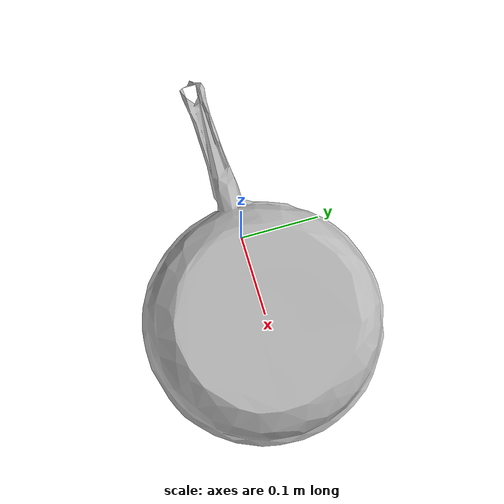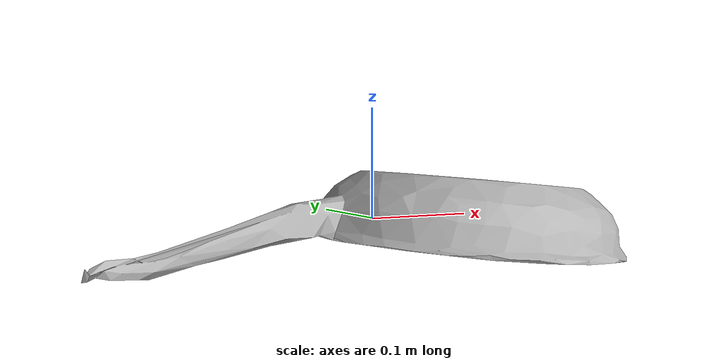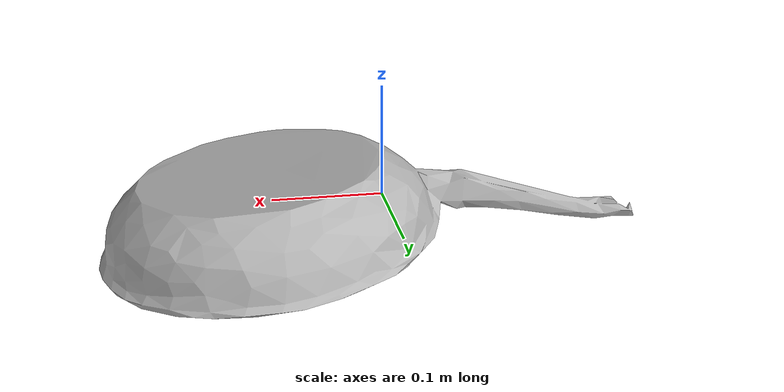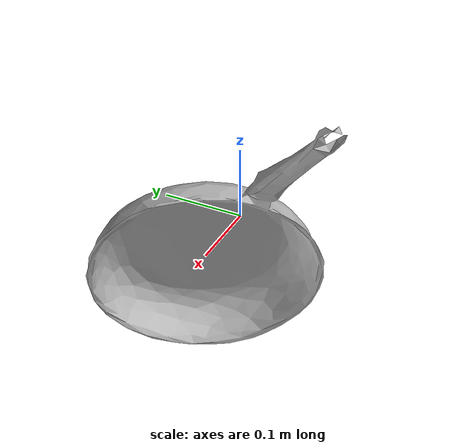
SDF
<?xml version='1.0'?>
<sdf version='1.6'>
	<model name='frying_pan'>
	<static>false</static>
	<pose>0 0 0 0 0 0</pose>
		<link name='link'>
      <inertial>
        <mass>0.30</mass>
        <pose>0.04531253 -0.00064551 0.00026609 0 0 0</pose>
        <inertia>
          <ixx>3.11393020192130e-06</ixx>
          <ixy>0.0</ixy>
          <ixz>0.0</ixz>
          <iyy>0.000203980703664912</iyy>
          <iyz>0.0</iyz>
          <izz>0.000204877893174758</izz>
        </inertia>
      </inertial>

			<visual name='visual'>
				<geometry>
					<mesh>
						<uri>model://frying_pan/model3.dae</uri>
					</mesh>
				</geometry>
			</visual>
			<collision name='collision_0'>
				<pose>0.0562 -0.13179 -0.0101771 0 0 0</pose>
				<geometry>
					<sphere>
						<radius>0.00885976</radius>
					</sphere>
				</geometry>
			</collision>
			<collision name='collision_1'>
				<pose>0.0451726 -0.134478 -0.0212358 0 0 0</pose>
				<geometry>
					<sphere>
						<radius>0.00728536</radius>
					</sphere>
				</geometry>
			</collision>
			<collision name='collision_2'>
				<pose>0.0693985 -0.132545 -0.00132962 0 0 0</pose>
				<geometry>
					<sphere>
						<radius>0.00721834</radius>
					</sphere>
				</geometry>
			</collision>
			<collision name='collision_3'>
				<pose>0.0713812 -0.135862 -0.0103313 0 0 0</pose>
				<geometry>
					<sphere>
						<radius>0.0083142</radius>
					</sphere>
				</geometry>
			</collision>
			<collision name='collision_4'>
				<pose>0.0614203 -0.126755 0.00715523 0 0 0</pose>
				<geometry>
					<sphere>
						<radius>0.00587204</radius>
					</sphere>
				</geometry>
			</collision>
			<collision name='collision_5'>
				<pose>0.0592254 -0.138391 -0.0220217 0 0 0</pose>
				<geometry>
					<sphere>
						<radius>0.00686</radius>
					</sphere>
				</geometry>
			</collision>
			<collision name='collision_6'>
				<pose>0.0714081 -0.139501 -0.0208494 0 0 0</pose>
				<geometry>
					<sphere>
						<radius>0.00783071</radius>
					</sphere>
				</geometry>
			</collision>
			<collision name='collision_7'>
				<pose>0.0560025 -0.129402 -0.000737161 0 0 0</pose>
				<geometry>
					<sphere>
						<radius>0.00686063</radius>
					</sphere>
				</geometry>
			</collision>
			<collision name='collision_8'>
				<pose>0.121417 -0.140401 -0.0253256 0 0 0</pose>
				<geometry>
					<sphere>
						<radius>0.00919308</radius>
					</sphere>
				</geometry>
			</collision>
			<collision name='collision_9'>
				<pose>0.0948804 -0.131211 0.00709508 0 0 0</pose>
				<geometry>
					<sphere>
						<radius>0.0103347</radius>
					</sphere>
				</geometry>
			</collision>
			<collision name='collision_10'>
				<pose>0.0853877 -0.144949 -0.0246931 0 0 0</pose>
				<geometry>
					<sphere>
						<radius>0.0134554</radius>
					</sphere>
				</geometry>
			</collision>
			<collision name='collision_11'>
				<pose>0.0828748 -0.136822 -0.00687217 0 0 0</pose>
				<geometry>
					<sphere>
						<radius>0.0146467</radius>
					</sphere>
				</geometry>
			</collision>
			<collision name='collision_12'>
				<pose>0.114605 -0.136456 -0.0071889 0 0 0</pose>
				<geometry>
					<sphere>
						<radius>0.0101895</radius>
					</sphere>
				</geometry>
			</collision>
			<collision name='collision_13'>
				<pose>0.108909 -0.142116 -0.0245372 0 0 0</pose>
				<geometry>
					<sphere>
						<radius>0.00972751</radius>
					</sphere>
				</geometry>
			</collision>
			<collision name='collision_14'>
				<pose>0.10134 -0.138801 -0.0120554 0 0 0</pose>
				<geometry>
					<sphere>
						<radius>0.0116466</radius>
					</sphere>
				</geometry>
			</collision>
			<collision name='collision_15'>
				<pose>0.112835 -0.130956 0.00644973 0 0 0</pose>
				<geometry>
					<sphere>
						<radius>0.0120146</radius>
					</sphere>
				</geometry>
			</collision>
			<collision name='collision_16'>
				<pose>0.0865979 -0.0761235 0.0298589 0 0 0</pose>
				<geometry>
					<sphere>
						<radius>0.0166086</radius>
					</sphere>
				</geometry>
			</collision>
			<collision name='collision_17'>
				<pose>0.109657 -0.0964192 0.0275544 0 0 0</pose>
				<geometry>
					<sphere>
						<radius>0.0147068</radius>
					</sphere>
				</geometry>
			</collision>
			<collision name='collision_18'>
				<pose>0.0934953 -0.102403 0.0287724 0 0 0</pose>
				<geometry>
					<sphere>
						<radius>0.011519</radius>
					</sphere>
				</geometry>
			</collision>
			<collision name='collision_19'>
				<pose>0.0787144 -0.0964121 0.0303655 0 0 0</pose>
				<geometry>
					<sphere>
						<radius>0.0118879</radius>
					</sphere>
				</geometry>
			</collision>
			<collision name='collision_20'>
				<pose>0.109677 -0.120818 0.0168308 0 0 0</pose>
				<geometry>
					<sphere>
						<radius>0.0116481</radius>
					</sphere>
				</geometry>
			</collision>
			<collision name='collision_21'>
				<pose>0.0713748 -0.123013 0.0157164 0 0 0</pose>
				<geometry>
					<sphere>
						<radius>0.0166641</radius>
					</sphere>
				</geometry>
			</collision>
			<collision name='collision_22'>
				<pose>0.0943768 -0.117271 0.0207511 0 0 0</pose>
				<geometry>
					<sphere>
						<radius>0.013141</radius>
					</sphere>
				</geometry>
			</collision>
			<collision name='collision_23'>
				<pose>0.0715633 -0.111171 0.023705 0 0 0</pose>
				<geometry>
					<sphere>
						<radius>0.0113743</radius>
					</sphere>
				</geometry>
			</collision>
			<collision name='collision_24'>
				<pose>0.174563 -0.121886 -0.0310723 0 0 0</pose>
				<geometry>
					<sphere>
						<radius>0.00809405</radius>
					</sphere>
				</geometry>
			</collision>
			<collision name='collision_25'>
				<pose>0.169407 -0.120988 -0.0194737 0 0 0</pose>
				<geometry>
					<sphere>
						<radius>0.00706917</radius>
					</sphere>
				</geometry>
			</collision>
			<collision name='collision_26'>
				<pose>0.170542 -0.118112 -0.010802 0 0 0</pose>
				<geometry>
					<sphere>
						<radius>0.00921118</radius>
					</sphere>
				</geometry>
			</collision>
			<collision name='collision_27'>
				<pose>0.18494 -0.117295 -0.0331302 0 0 0</pose>
				<geometry>
					<sphere>
						<radius>0.00797627</radius>
					</sphere>
				</geometry>
			</collision>
			<collision name='collision_28'>
				<pose>0.179073 -0.105391 0.000647001 0 0 0</pose>
				<geometry>
					<sphere>
						<radius>0.00836537</radius>
					</sphere>
				</geometry>
			</collision>
			<collision name='collision_29'>
				<pose>0.190274 -0.0995484 -0.00403912 0 0 0</pose>
				<geometry>
					<sphere>
						<radius>0.00760676</radius>
					</sphere>
				</geometry>
			</collision>
			<collision name='collision_30'>
				<pose>0.167652 -0.111613 0.00364722 0 0 0</pose>
				<geometry>
					<sphere>
						<radius>0.0108956</radius>
					</sphere>
				</geometry>
			</collision>
			<collision name='collision_31'>
				<pose>0.180615 -0.113067 -0.0161209 0 0 0</pose>
				<geometry>
					<sphere>
						<radius>0.0108616</radius>
					</sphere>
				</geometry>
			</collision>
			<collision name='collision_32'>
				<pose>0.195481 -0.10664 -0.0330335 0 0 0</pose>
				<geometry>
					<sphere>
						<radius>0.0102876</radius>
					</sphere>
				</geometry>
			</collision>
			<collision name='collision_33'>
				<pose>0.204815 -0.0953927 -0.0310845 0 0 0</pose>
				<geometry>
					<sphere>
						<radius>0.00956367</radius>
					</sphere>
				</geometry>
			</collision>
			<collision name='collision_34'>
				<pose>0.204499 -0.0910063 -0.0176958 0 0 0</pose>
				<geometry>
					<sphere>
						<radius>0.00700124</radius>
					</sphere>
				</geometry>
			</collision>
			<collision name='collision_35'>
				<pose>0.191909 -0.101987 -0.0110636 0 0 0</pose>
				<geometry>
					<sphere>
						<radius>0.00741224</radius>
					</sphere>
				</geometry>
			</collision>
			<collision name='collision_36'>
				<pose>0.211983 -0.090763 -0.0354723 0 0 0</pose>
				<geometry>
					<sphere>
						<radius>0.00976204</radius>
					</sphere>
				</geometry>
			</collision>
			<collision name='collision_37'>
				<pose>0.200057 -0.0918417 -0.00658895 0 0 0</pose>
				<geometry>
					<sphere>
						<radius>0.00750572</radius>
					</sphere>
				</geometry>
			</collision>
			<collision name='collision_38'>
				<pose>0.189766 -0.107202 -0.021263 0 0 0</pose>
				<geometry>
					<sphere>
						<radius>0.00593626</radius>
					</sphere>
				</geometry>
			</collision>
			<collision name='collision_39'>
				<pose>0.198107 -0.0986312 -0.0206666 0 0 0</pose>
				<geometry>
					<sphere>
						<radius>0.00629364</radius>
					</sphere>
				</geometry>
			</collision>
			<collision name='collision_40'>
				<pose>0.0686652 -0.0166041 0.0335434 0 0 0</pose>
				<geometry>
					<sphere>
						<radius>0.00260287</radius>
					</sphere>
				</geometry>
			</collision>
			<collision name='collision_41'>
				<pose>0.157434 -0.114226 0.00803791 0 0 0</pose>
				<geometry>
					<sphere>
						<radius>0.0116222</radius>
					</sphere>
				</geometry>
			</collision>
			<collision name='collision_42'>
				<pose>0.125587 -0.0971862 0.0260303 0 0 0</pose>
				<geometry>
					<sphere>
						<radius>0.0100445</radius>
					</sphere>
				</geometry>
			</collision>
			<collision name='collision_43'>
				<pose>0.142669 -0.1238 0.00441193 0 0 0</pose>
				<geometry>
					<sphere>
						<radius>0.0110815</radius>
					</sphere>
				</geometry>
			</collision>
			<collision name='collision_44'>
				<pose>0.143552 -0.100028 0.0225148 0 0 0</pose>
				<geometry>
					<sphere>
						<radius>0.0108086</radius>
					</sphere>
				</geometry>
			</collision>
			<collision name='collision_45'>
				<pose>0.12257 -0.1127 0.019936 0 0 0</pose>
				<geometry>
					<sphere>
						<radius>0.0118215</radius>
					</sphere>
				</geometry>
			</collision>
			<collision name='collision_46'>
				<pose>0.128102 -0.12334 0.0108719 0 0 0</pose>
				<geometry>
					<sphere>
						<radius>0.0104917</radius>
					</sphere>
				</geometry>
			</collision>
			<collision name='collision_47'>
				<pose>0.158975 -0.104905 0.0144664 0 0 0</pose>
				<geometry>
					<sphere>
						<radius>0.00812124</radius>
					</sphere>
				</geometry>
			</collision>
			<collision name='collision_48'>
				<pose>0.141204 -0.108339 0.0185582 0 0 0</pose>
				<geometry>
					<sphere>
						<radius>0.00979864</radius>
					</sphere>
				</geometry>
			</collision>
			<collision name='collision_49'>
				<pose>0.138108 -0.132482 -0.010115 0 0 0</pose>
				<geometry>
					<sphere>
						<radius>0.00982643</radius>
					</sphere>
				</geometry>
			</collision>
			<collision name='collision_50'>
				<pose>0.12845 -0.133506 -0.00530853 0 0 0</pose>
				<geometry>
					<sphere>
						<radius>0.0101618</radius>
					</sphere>
				</geometry>
			</collision>
			<collision name='collision_51'>
				<pose>0.156793 -0.125284 -0.00851876 0 0 0</pose>
				<geometry>
					<sphere>
						<radius>0.0096926</radius>
					</sphere>
				</geometry>
			</collision>
			<collision name='collision_52'>
				<pose>0.152206 -0.132997 -0.0301454 0 0 0</pose>
				<geometry>
					<sphere>
						<radius>0.00690099</radius>
					</sphere>
				</geometry>
			</collision>
			<collision name='collision_53'>
				<pose>0.129664 -0.139034 -0.0260367 0 0 0</pose>
				<geometry>
					<sphere>
						<radius>0.0088236</radius>
					</sphere>
				</geometry>
			</collision>
			<collision name='collision_54'>
				<pose>0.163246 -0.126267 -0.0273252 0 0 0</pose>
				<geometry>
					<sphere>
						<radius>0.0102302</radius>
					</sphere>
				</geometry>
			</collision>
			<collision name='collision_55'>
				<pose>0.151364 -0.130002 -0.018424 0 0 0</pose>
				<geometry>
					<sphere>
						<radius>0.00822348</radius>
					</sphere>
				</geometry>
			</collision>
			<collision name='collision_56'>
				<pose>0.140102 -0.13579 -0.0264808 0 0 0</pose>
				<geometry>
					<sphere>
						<radius>0.00780863</radius>
					</sphere>
				</geometry>
			</collision>
			<collision name='collision_57'>
				<pose>0.0383411 -0.12355 -0.00492877 0 0 0</pose>
				<geometry>
					<sphere>
						<radius>0.013357</radius>
					</sphere>
				</geometry>
			</collision>
			<collision name='collision_58'>
				<pose>0.0315417 -0.110529 0.0128072 0 0 0</pose>
				<geometry>
					<sphere>
						<radius>0.0105481</radius>
					</sphere>
				</geometry>
			</collision>
			<collision name='collision_59'>
				<pose>0.026785 -0.116563 -0.00417871 0 0 0</pose>
				<geometry>
					<sphere>
						<radius>0.00977577</radius>
					</sphere>
				</geometry>
			</collision>
			<collision name='collision_60'>
				<pose>0.0114686 -0.107684 -0.00899361 0 0 0</pose>
				<geometry>
					<sphere>
						<radius>0.00937851</radius>
					</sphere>
				</geometry>
			</collision>
			<collision name='collision_61'>
				<pose>0.0469204 -0.120129 0.00980874 0 0 0</pose>
				<geometry>
					<sphere>
						<radius>0.0097317</radius>
					</sphere>
				</geometry>
			</collision>
			<collision name='collision_62'>
				<pose>0.0312017 -0.127366 -0.019111 0 0 0</pose>
				<geometry>
					<sphere>
						<radius>0.0104007</radius>
					</sphere>
				</geometry>
			</collision>
			<collision name='collision_63'>
				<pose>0.0169883 -0.105365 0.00721311 0 0 0</pose>
				<geometry>
					<sphere>
						<radius>0.00948333</radius>
					</sphere>
				</geometry>
			</collision>
			<collision name='collision_64'>
				<pose>0.0173636 -0.117408 -0.017319 0 0 0</pose>
				<geometry>
					<sphere>
						<radius>0.00822931</radius>
					</sphere>
				</geometry>
			</collision>
			<collision name='collision_65'>
				<pose>-0.0614453 -0.000608853 -0.00111196 0 0 0</pose>
				<geometry>
					<sphere>
						<radius>0.0203778</radius>
					</sphere>
				</geometry>
			</collision>
			<collision name='collision_66'>
				<pose>-0.0748924 -0.000945637 -0.000696014 0 0 0</pose>
				<geometry>
					<sphere>
						<radius>0.0204321</radius>
					</sphere>
				</geometry>
			</collision>
			<collision name='collision_67'>
				<pose>-0.0417241 -0.0203183 -0.00966566 0 0 0</pose>
				<geometry>
					<sphere>
						<radius>0.00702979</radius>
					</sphere>
				</geometry>
			</collision>
			<collision name='collision_68'>
				<pose>-0.0487356 -0.00189691 0.000205616 0 0 0</pose>
				<geometry>
					<sphere>
						<radius>0.0208907</radius>
					</sphere>
				</geometry>
			</collision>
			<collision name='collision_69'>
				<pose>-0.0393961 -0.0136143 0.00383451 0 0 0</pose>
				<geometry>
					<sphere>
						<radius>0.00890397</radius>
					</sphere>
				</geometry>
			</collision>
			<collision name='collision_70'>
				<pose>-0.0421056 -0.0294922 -0.0129318 0 0 0</pose>
				<geometry>
					<sphere>
						<radius>0.00619636</radius>
					</sphere>
				</geometry>
			</collision>
			<collision name='collision_71'>
				<pose>-0.0409525 0.0165174 -0.00544789 0 0 0</pose>
				<geometry>
					<sphere>
						<radius>0.00426496</radius>
					</sphere>
				</geometry>
			</collision>
			<collision name='collision_72'>
				<pose>-0.0448498 0.018299 -0.0105834 0 0 0</pose>
				<geometry>
					<sphere>
						<radius>0.00744359</radius>
					</sphere>
				</geometry>
			</collision>
			<collision name='collision_73'>
				<pose>-0.0148645 -0.0552237 0.0194479 0 0 0</pose>
				<geometry>
					<sphere>
						<radius>0.0137431</radius>
					</sphere>
				</geometry>
			</collision>
			<collision name='collision_74'>
				<pose>-0.0345052 -0.0415625 -0.00533415 0 0 0</pose>
				<geometry>
					<sphere>
						<radius>0.013909</radius>
					</sphere>
				</geometry>
			</collision>
			<collision name='collision_75'>
				<pose>-0.019166 -0.0574719 0.0115452 0 0 0</pose>
				<geometry>
					<sphere>
						<radius>0.0113321</radius>
					</sphere>
				</geometry>
			</collision>
			<collision name='collision_76'>
				<pose>-0.00238807 -0.0519755 0.028803 0 0 0</pose>
				<geometry>
					<sphere>
						<radius>0.0127269</radius>
					</sphere>
				</geometry>
			</collision>
			<collision name='collision_77'>
				<pose>0.000434022 -0.0664044 0.0258613 0 0 0</pose>
				<geometry>
					<sphere>
						<radius>0.00843029</radius>
					</sphere>
				</geometry>
			</collision>
			<collision name='collision_78'>
				<pose>-0.0265745 -0.0406795 0.0112616 0 0 0</pose>
				<geometry>
					<sphere>
						<radius>0.00887068</radius>
					</sphere>
				</geometry>
			</collision>
			<collision name='collision_79'>
				<pose>-0.0344523 -0.0278603 0.00129704 0 0 0</pose>
				<geometry>
					<sphere>
						<radius>0.00942515</radius>
					</sphere>
				</geometry>
			</collision>
			<collision name='collision_80'>
				<pose>-0.0280156 -0.0638522 -0.0115429 0 0 0</pose>
				<geometry>
					<sphere>
						<radius>0.014628</radius>
					</sphere>
				</geometry>
			</collision>
			<collision name='collision_81'>
				<pose>0.043988 0.00842946 0.0336388 0 0 0</pose>
				<geometry>
					<sphere>
						<radius>0.0152909</radius>
					</sphere>
				</geometry>
			</collision>
			<collision name='collision_82'>
				<pose>0.0567133 -0.0343417 0.0325859 0 0 0</pose>
				<geometry>
					<sphere>
						<radius>0.0147539</radius>
					</sphere>
				</geometry>
			</collision>
			<collision name='collision_83'>
				<pose>0.0625762 -0.0127908 0.0318541 0 0 0</pose>
				<geometry>
					<sphere>
						<radius>0.014897</radius>
					</sphere>
				</geometry>
			</collision>
			<collision name='collision_84'>
				<pose>0.0353104 -0.0335118 0.034672 0 0 0</pose>
				<geometry>
					<sphere>
						<radius>0.0104983</radius>
					</sphere>
				</geometry>
			</collision>
			<collision name='collision_85'>
				<pose>0.0136996 -0.0351575 0.035817 0 0 0</pose>
				<geometry>
					<sphere>
						<radius>0.0184496</radius>
					</sphere>
				</geometry>
			</collision>
			<collision name='collision_86'>
				<pose>0.0367157 -0.0162408 0.0344297 0 0 0</pose>
				<geometry>
					<sphere>
						<radius>0.0127896</radius>
					</sphere>
				</geometry>
			</collision>
			<collision name='collision_87'>
				<pose>0.0283339 -0.009278 0.0352214 0 0 0</pose>
				<geometry>
					<sphere>
						<radius>0.0111142</radius>
					</sphere>
				</geometry>
			</collision>
			<collision name='collision_88'>
				<pose>0.0277854 0.0125226 0.0351895 0 0 0</pose>
				<geometry>
					<sphere>
						<radius>0.0116575</radius>
					</sphere>
				</geometry>
			</collision>
			<collision name='collision_89'>
				<pose>-0.0189833 -0.0332899 0.0232848 0 0 0</pose>
				<geometry>
					<sphere>
						<radius>0.0119638</radius>
					</sphere>
				</geometry>
			</collision>
			<collision name='collision_90'>
				<pose>0.00797632 -0.0128078 0.0365319 0 0 0</pose>
				<geometry>
					<sphere>
						<radius>0.0137247</radius>
					</sphere>
				</geometry>
			</collision>
			<collision name='collision_91'>
				<pose>-0.000314139 -0.0316849 0.0338534 0 0 0</pose>
				<geometry>
					<sphere>
						<radius>0.014415</radius>
					</sphere>
				</geometry>
			</collision>
			<collision name='collision_92'>
				<pose>-0.0307867 -0.016409 0.0140346 0 0 0</pose>
				<geometry>
					<sphere>
						<radius>0.0112373</radius>
					</sphere>
				</geometry>
			</collision>
			<collision name='collision_93'>
				<pose>0.00958963 0.00336274 0.0364063 0 0 0</pose>
				<geometry>
					<sphere>
						<radius>0.0158265</radius>
					</sphere>
				</geometry>
			</collision>
			<collision name='collision_94'>
				<pose>-0.0150015 0.00287171 0.0295745 0 0 0</pose>
				<geometry>
					<sphere>
						<radius>0.0158164</radius>
					</sphere>
				</geometry>
			</collision>
			<collision name='collision_95'>
				<pose>-0.0316445 0.00124975 0.017005 0 0 0</pose>
				<geometry>
					<sphere>
						<radius>0.0126823</radius>
					</sphere>
				</geometry>
			</collision>
			<collision name='collision_96'>
				<pose>-0.0141825 -0.0131097 0.0295949 0 0 0</pose>
				<geometry>
					<sphere>
						<radius>0.0113195</radius>
					</sphere>
				</geometry>
			</collision>
			<collision name='collision_97'>
				<pose>0.0633735 -0.0460143 0.0320086 0 0 0</pose>
				<geometry>
					<sphere>
						<radius>0.0112514</radius>
					</sphere>
				</geometry>
			</collision>
			<collision name='collision_98'>
				<pose>0.0651944 -0.0789146 0.031961 0 0 0</pose>
				<geometry>
					<sphere>
						<radius>0.0121216</radius>
					</sphere>
				</geometry>
			</collision>
			<collision name='collision_99'>
				<pose>0.0335054 -0.0713974 0.0343823 0 0 0</pose>
				<geometry>
					<sphere>
						<radius>0.0113452</radius>
					</sphere>
				</geometry>
			</collision>
			<collision name='collision_100'>
				<pose>0.0223229 -0.0529001 0.0355373 0 0 0</pose>
				<geometry>
					<sphere>
						<radius>0.0119241</radius>
					</sphere>
				</geometry>
			</collision>
			<collision name='collision_101'>
				<pose>0.0430045 -0.0500627 0.0340005 0 0 0</pose>
				<geometry>
					<sphere>
						<radius>0.0139618</radius>
					</sphere>
				</geometry>
			</collision>
			<collision name='collision_102'>
				<pose>0.0120726 -0.0673178 0.0309656 0 0 0</pose>
				<geometry>
					<sphere>
						<radius>0.0129661</radius>
					</sphere>
				</geometry>
			</collision>
			<collision name='collision_103'>
				<pose>0.0500344 -0.0666749 0.0333908 0 0 0</pose>
				<geometry>
					<sphere>
						<radius>0.0119209</radius>
					</sphere>
				</geometry>
			</collision>
			<collision name='collision_104'>
				<pose>0.0690237 -0.0624091 0.031547 0 0 0</pose>
				<geometry>
					<sphere>
						<radius>0.0114159</radius>
					</sphere>
				</geometry>
			</collision>
			<collision name='collision_105'>
				<pose>0.0585684 -0.0994834 0.029156 0 0 0</pose>
				<geometry>
					<sphere>
						<radius>0.00895423</radius>
					</sphere>
				</geometry>
			</collision>
			<collision name='collision_106'>
				<pose>0.0264649 -0.0837548 0.0292752 0 0 0</pose>
				<geometry>
					<sphere>
						<radius>0.0108424</radius>
					</sphere>
				</geometry>
			</collision>
			<collision name='collision_107'>
				<pose>0.0624457 -0.0883689 0.0320674 0 0 0</pose>
				<geometry>
					<sphere>
						<radius>0.011215</radius>
					</sphere>
				</geometry>
			</collision>
			<collision name='collision_108'>
				<pose>0.0321939 -0.100016 0.0228125 0 0 0</pose>
				<geometry>
					<sphere>
						<radius>0.00918236</radius>
					</sphere>
				</geometry>
			</collision>
			<collision name='collision_109'>
				<pose>0.0439702 -0.105556 0.0229678 0 0 0</pose>
				<geometry>
					<sphere>
						<radius>0.0103904</radius>
					</sphere>
				</geometry>
			</collision>
			<collision name='collision_110'>
				<pose>0.0568675 -0.112098 0.0216381 0 0 0</pose>
				<geometry>
					<sphere>
						<radius>0.00988896</radius>
					</sphere>
				</geometry>
			</collision>
			<collision name='collision_111'>
				<pose>0.0442075 -0.087173 0.0325144 0 0 0</pose>
				<geometry>
					<sphere>
						<radius>0.0103169</radius>
					</sphere>
				</geometry>
			</collision>
			<collision name='collision_112'>
				<pose>0.0177669 -0.092921 0.0210252 0 0 0</pose>
				<geometry>
					<sphere>
						<radius>0.0121699</radius>
					</sphere>
				</geometry>
			</collision>
			<collision name='collision_113'>
				<pose>0.00309868 -0.093829 0.00446192 0 0 0</pose>
				<geometry>
					<sphere>
						<radius>0.0114506</radius>
					</sphere>
				</geometry>
			</collision>
			<collision name='collision_114'>
				<pose>0.00310722 -0.105767 -0.0156246 0 0 0</pose>
				<geometry>
					<sphere>
						<radius>0.012924</radius>
					</sphere>
				</geometry>
			</collision>
			<collision name='collision_115'>
				<pose>-0.0190223 -0.0742453 -0.00682121 0 0 0</pose>
				<geometry>
					<sphere>
						<radius>0.0117121</radius>
					</sphere>
				</geometry>
			</collision>
			<collision name='collision_116'>
				<pose>-0.00595504 -0.0966541 -0.0156494 0 0 0</pose>
				<geometry>
					<sphere>
						<radius>0.00815717</radius>
					</sphere>
				</geometry>
			</collision>
			<collision name='collision_117'>
				<pose>-0.00983171 -0.0722447 0.0133682 0 0 0</pose>
				<geometry>
					<sphere>
						<radius>0.0113168</radius>
					</sphere>
				</geometry>
			</collision>
			<collision name='collision_118'>
				<pose>-0.0123457 -0.0872332 -0.0109546 0 0 0</pose>
				<geometry>
					<sphere>
						<radius>0.0115798</radius>
					</sphere>
				</geometry>
			</collision>
			<collision name='collision_119'>
				<pose>-0.0061562 -0.0841213 0.00518405 0 0 0</pose>
				<geometry>
					<sphere>
						<radius>0.00649805</radius>
					</sphere>
				</geometry>
			</collision>
			<collision name='collision_120'>
				<pose>0.00588717 -0.0832073 0.0189373 0 0 0</pose>
				<geometry>
					<sphere>
						<radius>0.0111114</radius>
					</sphere>
				</geometry>
			</collision>
			<collision name='collision_121'>
				<pose>0.161174 0.0385847 0.0222601 0 0 0</pose>
				<geometry>
					<sphere>
						<radius>0.0151495</radius>
					</sphere>
				</geometry>
			</collision>
			<collision name='collision_122'>
				<pose>0.176529 0.0478207 0.020855 0 0 0</pose>
				<geometry>
					<sphere>
						<radius>0.0120239</radius>
					</sphere>
				</geometry>
			</collision>
			<collision name='collision_123'>
				<pose>0.177454 0.0808129 0.0178112 0 0 0</pose>
				<geometry>
					<sphere>
						<radius>0.0125479</radius>
					</sphere>
				</geometry>
			</collision>
			<collision name='collision_124'>
				<pose>0.163018 0.0650367 0.0220972 0 0 0</pose>
				<geometry>
					<sphere>
						<radius>0.0135352</radius>
					</sphere>
				</geometry>
			</collision>
			<collision name='collision_125'>
				<pose>0.158894 0.0523417 0.0224836 0 0 0</pose>
				<geometry>
					<sphere>
						<radius>0.00841523</radius>
					</sphere>
				</geometry>
			</collision>
			<collision name='collision_126'>
				<pose>0.196473 0.0576588 0.0158813 0 0 0</pose>
				<geometry>
					<sphere>
						<radius>0.0112676</radius>
					</sphere>
				</geometry>
			</collision>
			<collision name='collision_127'>
				<pose>0.192948 0.0750183 0.0118879 0 0 0</pose>
				<geometry>
					<sphere>
						<radius>0.0099322</radius>
					</sphere>
				</geometry>
			</collision>
			<collision name='collision_128'>
				<pose>0.184184 0.0614393 0.0198801 0 0 0</pose>
				<geometry>
					<sphere>
						<radius>0.00974044</radius>
					</sphere>
				</geometry>
			</collision>
			<collision name='collision_129'>
				<pose>0.215869 0.0689042 -0.0101107 0 0 0</pose>
				<geometry>
					<sphere>
						<radius>0.0105269</radius>
					</sphere>
				</geometry>
			</collision>
			<collision name='collision_130'>
				<pose>0.224252 0.0685608 -0.0338435 0 0 0</pose>
				<geometry>
					<sphere>
						<radius>0.0122275</radius>
					</sphere>
				</geometry>
			</collision>
			<collision name='collision_131'>
				<pose>0.21409 0.0851496 -0.0350173 0 0 0</pose>
				<geometry>
					<sphere>
						<radius>0.0091981</radius>
					</sphere>
				</geometry>
			</collision>
			<collision name='collision_132'>
				<pose>0.199095 0.0822059 0.00125508 0 0 0</pose>
				<geometry>
					<sphere>
						<radius>0.0142612</radius>
					</sphere>
				</geometry>
			</collision>
			<collision name='collision_133'>
				<pose>0.203504 0.0681511 0.00650783 0 0 0</pose>
				<geometry>
					<sphere>
						<radius>0.0117865</radius>
					</sphere>
				</geometry>
			</collision>
			<collision name='collision_134'>
				<pose>0.202563 0.0981163 -0.0333969 0 0 0</pose>
				<geometry>
					<sphere>
						<radius>0.00964617</radius>
					</sphere>
				</geometry>
			</collision>
			<collision name='collision_135'>
				<pose>0.209668 0.0836904 -0.0196413 0 0 0</pose>
				<geometry>
					<sphere>
						<radius>0.010567</radius>
					</sphere>
				</geometry>
			</collision>
			<collision name='collision_136'>
				<pose>0.215953 0.0759262 -0.0228905 0 0 0</pose>
				<geometry>
					<sphere>
						<radius>0.00703173</radius>
					</sphere>
				</geometry>
			</collision>
			<collision name='collision_137'>
				<pose>0.117262 0.133817 -0.000896288 0 0 0</pose>
				<geometry>
					<sphere>
						<radius>0.00826675</radius>
					</sphere>
				</geometry>
			</collision>
			<collision name='collision_138'>
				<pose>0.121818 0.140378 -0.0265529 0 0 0</pose>
				<geometry>
					<sphere>
						<radius>0.00911823</radius>
					</sphere>
				</geometry>
			</collision>
			<collision name='collision_139'>
				<pose>0.124393 0.136142 -0.0115779 0 0 0</pose>
				<geometry>
					<sphere>
						<radius>0.00763559</radius>
					</sphere>
				</geometry>
			</collision>
			<collision name='collision_140'>
				<pose>0.134918 0.135723 -0.023347 0 0 0</pose>
				<geometry>
					<sphere>
						<radius>0.00959796</radius>
					</sphere>
				</geometry>
			</collision>
			<collision name='collision_141'>
				<pose>0.132989 0.130374 -0.000978828 0 0 0</pose>
				<geometry>
					<sphere>
						<radius>0.00915688</radius>
					</sphere>
				</geometry>
			</collision>
			<collision name='collision_142'>
				<pose>0.109506 0.140165 -0.0180951 0 0 0</pose>
				<geometry>
					<sphere>
						<radius>0.0115156</radius>
					</sphere>
				</geometry>
			</collision>
			<collision name='collision_143'>
				<pose>0.105167 0.13499 -0.00155803 0 0 0</pose>
				<geometry>
					<sphere>
						<radius>0.00599527</radius>
					</sphere>
				</geometry>
			</collision>
			<collision name='collision_144'>
				<pose>0.137088 0.132796 -0.0121472 0 0 0</pose>
				<geometry>
					<sphere>
						<radius>0.00703481</radius>
					</sphere>
				</geometry>
			</collision>
			<collision name='collision_145'>
				<pose>0.114111 0.075529 0.0267321 0 0 0</pose>
				<geometry>
					<sphere>
						<radius>0.00870474</radius>
					</sphere>
				</geometry>
			</collision>
			<collision name='collision_146'>
				<pose>0.117935 0.089318 0.0263637 0 0 0</pose>
				<geometry>
					<sphere>
						<radius>0.0145876</radius>
					</sphere>
				</geometry>
			</collision>
			<collision name='collision_147'>
				<pose>0.132865 0.0584387 0.0249355 0 0 0</pose>
				<geometry>
					<sphere>
						<radius>0.00961836</radius>
					</sphere>
				</geometry>
			</collision>
			<collision name='collision_148'>
				<pose>0.137118 0.0412837 0.0245217 0 0 0</pose>
				<geometry>
					<sphere>
						<radius>0.0124876</radius>
					</sphere>
				</geometry>
			</collision>
			<collision name='collision_149'>
				<pose>0.116376 0.0485033 0.0264983 0 0 0</pose>
				<geometry>
					<sphere>
						<radius>0.0116101</radius>
					</sphere>
				</geometry>
			</collision>
			<collision name='collision_150'>
				<pose>0.145575 0.0635139 0.0237299 0 0 0</pose>
				<geometry>
					<sphere>
						<radius>0.015191</radius>
					</sphere>
				</geometry>
			</collision>
			<collision name='collision_151'>
				<pose>0.119461 0.0621989 0.026218 0 0 0</pose>
				<geometry>
					<sphere>
						<radius>0.00954545</radius>
					</sphere>
				</geometry>
			</collision>
			<collision name='collision_152'>
				<pose>0.131669 0.0769156 0.0250587 0 0 0</pose>
				<geometry>
					<sphere>
						<radius>0.0111696</radius>
					</sphere>
				</geometry>
			</collision>
			<collision name='collision_153'>
				<pose>0.140164 0.0971698 0.0236866 0 0 0</pose>
				<geometry>
					<sphere>
						<radius>0.0137395</radius>
					</sphere>
				</geometry>
			</collision>
			<collision name='collision_154'>
				<pose>0.161881 0.113707 0.00435799 0 0 0</pose>
				<geometry>
					<sphere>
						<radius>0.0122617</radius>
					</sphere>
				</geometry>
			</collision>
			<collision name='collision_155'>
				<pose>0.157171 0.0825627 0.0226531 0 0 0</pose>
				<geometry>
					<sphere>
						<radius>0.00881787</radius>
					</sphere>
				</geometry>
			</collision>
			<collision name='collision_156'>
				<pose>0.166421 0.0989136 0.0136965 0 0 0</pose>
				<geometry>
					<sphere>
						<radius>0.0121136</radius>
					</sphere>
				</geometry>
			</collision>
			<collision name='collision_157'>
				<pose>0.169364 0.086748 0.0189105 0 0 0</pose>
				<geometry>
					<sphere>
						<radius>0.0101467</radius>
					</sphere>
				</geometry>
			</collision>
			<collision name='collision_158'>
				<pose>0.153806 0.0938428 0.0214567 0 0 0</pose>
				<geometry>
					<sphere>
						<radius>0.00684478</radius>
					</sphere>
				</geometry>
			</collision>
			<collision name='collision_159'>
				<pose>0.14469 0.110359 0.0150248 0 0 0</pose>
				<geometry>
					<sphere>
						<radius>0.0122627</radius>
					</sphere>
				</geometry>
			</collision>
			<collision name='collision_160'>
				<pose>0.145177 0.0834814 0.0237853 0 0 0</pose>
				<geometry>
					<sphere>
						<radius>0.0091546</radius>
					</sphere>
				</geometry>
			</collision>
			<collision name='collision_161'>
				<pose>0.168704 0.118348 -0.00953498 0 0 0</pose>
				<geometry>
					<sphere>
						<radius>0.0118372</radius>
					</sphere>
				</geometry>
			</collision>
			<collision name='collision_162'>
				<pose>0.16392 0.125253 -0.0263772 0 0 0</pose>
				<geometry>
					<sphere>
						<radius>0.0100297</radius>
					</sphere>
				</geometry>
			</collision>
			<collision name='collision_163'>
				<pose>0.157664 0.123838 -0.00787257 0 0 0</pose>
				<geometry>
					<sphere>
						<radius>0.00752018</radius>
					</sphere>
				</geometry>
			</collision>
			<collision name='collision_164'>
				<pose>0.141298 0.123904 0.00427687 0 0 0</pose>
				<geometry>
					<sphere>
						<radius>0.00929725</radius>
					</sphere>
				</geometry>
			</collision>
			<collision name='collision_165'>
				<pose>0.149638 0.128988 -0.0144044 0 0 0</pose>
				<geometry>
					<sphere>
						<radius>0.00832701</radius>
					</sphere>
				</geometry>
			</collision>
			<collision name='collision_166'>
				<pose>0.151033 0.13251 -0.0293718 0 0 0</pose>
				<geometry>
					<sphere>
						<radius>0.0106145</radius>
					</sphere>
				</geometry>
			</collision>
			<collision name='collision_167'>
				<pose>0.137171 0.137388 -0.0288286 0 0 0</pose>
				<geometry>
					<sphere>
						<radius>0.00515637</radius>
					</sphere>
				</geometry>
			</collision>
			<collision name='collision_168'>
				<pose>0.149032 0.125126 -0.00182787 0 0 0</pose>
				<geometry>
					<sphere>
						<radius>0.00693251</radius>
					</sphere>
				</geometry>
			</collision>
			<collision name='collision_169'>
				<pose>0.126811 0.107538 0.0217238 0 0 0</pose>
				<geometry>
					<sphere>
						<radius>0.0105103</radius>
					</sphere>
				</geometry>
			</collision>
			<collision name='collision_170'>
				<pose>0.108951 0.102602 0.0266706 0 0 0</pose>
				<geometry>
					<sphere>
						<radius>0.00936054</radius>
					</sphere>
				</geometry>
			</collision>
			<collision name='collision_171'>
				<pose>0.107869 0.111925 0.0215291 0 0 0</pose>
				<geometry>
					<sphere>
						<radius>0.0100745</radius>
					</sphere>
				</geometry>
			</collision>
			<collision name='collision_172'>
				<pose>0.124981 0.120239 0.0138536 0 0 0</pose>
				<geometry>
					<sphere>
						<radius>0.0104361</radius>
					</sphere>
				</geometry>
			</collision>
			<collision name='collision_173'>
				<pose>0.104615 0.130402 0.00742742 0 0 0</pose>
				<geometry>
					<sphere>
						<radius>0.0097845</radius>
					</sphere>
				</geometry>
			</collision>
			<collision name='collision_174'>
				<pose>0.118772 0.102139 0.0257031 0 0 0</pose>
				<geometry>
					<sphere>
						<radius>0.00870634</radius>
					</sphere>
				</geometry>
			</collision>
			<collision name='collision_175'>
				<pose>0.120786 0.126182 0.0093654 0 0 0</pose>
				<geometry>
					<sphere>
						<radius>0.00949111</radius>
					</sphere>
				</geometry>
			</collision>
			<collision name='collision_176'>
				<pose>0.10367 0.121482 0.0157528 0 0 0</pose>
				<geometry>
					<sphere>
						<radius>0.00942171</radius>
					</sphere>
				</geometry>
			</collision>
			<collision name='collision_177'>
				<pose>0.192996 0.106028 -0.0300055 0 0 0</pose>
				<geometry>
					<sphere>
						<radius>0.0120461</radius>
					</sphere>
				</geometry>
			</collision>
			<collision name='collision_178'>
				<pose>0.201679 0.0929738 -0.0163089 0 0 0</pose>
				<geometry>
					<sphere>
						<radius>0.0100929</radius>
					</sphere>
				</geometry>
			</collision>
			<collision name='collision_179'>
				<pose>0.19417 0.0913154 -0.00098337 0 0 0</pose>
				<geometry>
					<sphere>
						<radius>0.00692024</radius>
					</sphere>
				</geometry>
			</collision>
			<collision name='collision_180'>
				<pose>0.188929 0.103019 -0.0100776 0 0 0</pose>
				<geometry>
					<sphere>
						<radius>0.00937255</radius>
					</sphere>
				</geometry>
			</collision>
			<collision name='collision_181'>
				<pose>0.17586 0.109157 -0.00185965 0 0 0</pose>
				<geometry>
					<sphere>
						<radius>0.0095311</radius>
					</sphere>
				</geometry>
			</collision>
			<collision name='collision_182'>
				<pose>0.177567 0.117959 -0.0294406 0 0 0</pose>
				<geometry>
					<sphere>
						<radius>0.0117493</radius>
					</sphere>
				</geometry>
			</collision>
			<collision name='collision_183'>
				<pose>0.181507 0.111543 -0.016248 0 0 0</pose>
				<geometry>
					<sphere>
						<radius>0.00655214</radius>
					</sphere>
				</geometry>
			</collision>
			<collision name='collision_184'>
				<pose>0.183287 0.0957143 0.00571524 0 0 0</pose>
				<geometry>
					<sphere>
						<radius>0.00975212</radius>
					</sphere>
				</geometry>
			</collision>
			<collision name='collision_185'>
				<pose>-0.166864 9.20857e-05 -0.0211658 0 0 0</pose>
				<geometry>
					<sphere>
						<radius>0.0116217</radius>
					</sphere>
				</geometry>
			</collision>
			<collision name='collision_186'>
				<pose>-0.155195 -0.00190631 -0.0182061 0 0 0</pose>
				<geometry>
					<sphere>
						<radius>0.0133892</radius>
					</sphere>
				</geometry>
			</collision>
			<collision name='collision_187'>
				<pose>-0.174704 -0.00953447 -0.0241959 0 0 0</pose>
				<geometry>
					<sphere>
						<radius>0.00723013</radius>
					</sphere>
				</geometry>
			</collision>
			<collision name='collision_188'>
				<pose>-0.1593 0.00416039 -0.0202904 0 0 0</pose>
				<geometry>
					<sphere>
						<radius>0.00943661</radius>
					</sphere>
				</geometry>
			</collision>
			<collision name='collision_189'>
				<pose>-0.162212 -0.0102033 -0.0199624 0 0 0</pose>
				<geometry>
					<sphere>
						<radius>0.00658957</radius>
					</sphere>
				</geometry>
			</collision>
			<collision name='collision_190'>
				<pose>-0.16303 -0.00830829 -0.0236989 0 0 0</pose>
				<geometry>
					<sphere>
						<radius>0.00600031</radius>
					</sphere>
				</geometry>
			</collision>
			<collision name='collision_191'>
				<pose>-0.171257 -0.0086164 -0.0249704 0 0 0</pose>
				<geometry>
					<sphere>
						<radius>0.00639327</radius>
					</sphere>
				</geometry>
			</collision>
			<collision name='collision_192'>
				<pose>-0.168976 -0.0123935 -0.0198826 0 0 0</pose>
				<geometry>
					<sphere>
						<radius>0.00363167</radius>
					</sphere>
				</geometry>
			</collision>
			<collision name='collision_193'>
				<pose>-0.0915791 -0.00374487 -0.0040139 0 0 0</pose>
				<geometry>
					<sphere>
						<radius>0.0150324</radius>
					</sphere>
				</geometry>
			</collision>
			<collision name='collision_194'>
				<pose>-0.102744 -0.00369957 -0.0059464 0 0 0</pose>
				<geometry>
					<sphere>
						<radius>0.0138431</radius>
					</sphere>
				</geometry>
			</collision>
			<collision name='collision_195'>
				<pose>-0.104591 0.00433314 -0.00665902 0 0 0</pose>
				<geometry>
					<sphere>
						<radius>0.0116408</radius>
					</sphere>
				</geometry>
			</collision>
			<collision name='collision_196'>
				<pose>-0.0913577 0.00384803 -0.00743969 0 0 0</pose>
				<geometry>
					<sphere>
						<radius>0.0122201</radius>
					</sphere>
				</geometry>
			</collision>
			<collision name='collision_197'>
				<pose>-0.0902442 0.00826418 0.0042069 0 0 0</pose>
				<geometry>
					<sphere>
						<radius>0.00573182</radius>
					</sphere>
				</geometry>
			</collision>
			<collision name='collision_198'>
				<pose>-0.0991291 0.00618032 -0.000652229 0 0 0</pose>
				<geometry>
					<sphere>
						<radius>0.00775839</radius>
					</sphere>
				</geometry>
			</collision>
			<collision name='collision_199'>
				<pose>-0.0924298 0.00624687 0.000888103 0 0 0</pose>
				<geometry>
					<sphere>
						<radius>0.00812989</radius>
					</sphere>
				</geometry>
			</collision>
			<collision name='collision_200'>
				<pose>-0.229533 -0.0168413 -0.0296206 0 0 0</pose>
				<geometry>
					<sphere>
						<radius>0.00480235</radius>
					</sphere>
				</geometry>
			</collision>
			<collision name='collision_201'>
				<pose>-0.239823 0.0075469 -0.0329934 0 0 0</pose>
				<geometry>
					<sphere>
						<radius>0.00571095</radius>
					</sphere>
				</geometry>
			</collision>
			<collision name='collision_202'>
				<pose>-0.235566 -0.0163087 -0.0298417 0 0 0</pose>
				<geometry>
					<sphere>
						<radius>0.00528624</radius>
					</sphere>
				</geometry>
			</collision>
			<collision name='collision_203'>
				<pose>-0.221477 -0.0155299 -0.0324883 0 0 0</pose>
				<geometry>
					<sphere>
						<radius>0.00616132</radius>
					</sphere>
				</geometry>
			</collision>
			<collision name='collision_204'>
				<pose>-0.243647 -0.00528721 -0.0333611 0 0 0</pose>
				<geometry>
					<sphere>
						<radius>0.00378863</radius>
					</sphere>
				</geometry>
			</collision>
			<collision name='collision_205'>
				<pose>-0.244534 -0.000876061 -0.0314642 0 0 0</pose>
				<geometry>
					<sphere>
						<radius>0.00565988</radius>
					</sphere>
				</geometry>
			</collision>
			<collision name='collision_206'>
				<pose>-0.246559 0.00505822 -0.0374897 0 0 0</pose>
				<geometry>
					<sphere>
						<radius>0.00143202</radius>
					</sphere>
				</geometry>
			</collision>
			<collision name='collision_207'>
				<pose>-0.21905 -0.0148261 -0.0270944 0 0 0</pose>
				<geometry>
					<sphere>
						<radius>0.00467204</radius>
					</sphere>
				</geometry>
			</collision>
			<collision name='collision_208'>
				<pose>-0.203213 -0.00836186 -0.0308609 0 0 0</pose>
				<geometry>
					<sphere>
						<radius>0.00968026</radius>
					</sphere>
				</geometry>
			</collision>
			<collision name='collision_209'>
				<pose>-0.202268 0.00305209 -0.0290489 0 0 0</pose>
				<geometry>
					<sphere>
						<radius>0.0104345</radius>
					</sphere>
				</geometry>
			</collision>
			<collision name='collision_210'>
				<pose>-0.215614 -0.0146678 -0.0279692 0 0 0</pose>
				<geometry>
					<sphere>
						<radius>0.00471825</radius>
					</sphere>
				</geometry>
			</collision>
			<collision name='collision_211'>
				<pose>-0.209933 0.00404309 -0.0278025 0 0 0</pose>
				<geometry>
					<sphere>
						<radius>0.00725539</radius>
					</sphere>
				</geometry>
			</collision>
			<collision name='collision_212'>
				<pose>-0.210252 -0.0122684 -0.0276902 0 0 0</pose>
				<geometry>
					<sphere>
						<radius>0.00562956</radius>
					</sphere>
				</geometry>
			</collision>
			<collision name='collision_213'>
				<pose>-0.213709 -0.0136797 -0.0335191 0 0 0</pose>
				<geometry>
					<sphere>
						<radius>0.0041395</radius>
					</sphere>
				</geometry>
			</collision>
			<collision name='collision_214'>
				<pose>-0.197881 -0.0112934 -0.0279503 0 0 0</pose>
				<geometry>
					<sphere>
						<radius>0.00625552</radius>
					</sphere>
				</geometry>
			</collision>
			<collision name='collision_215'>
				<pose>-0.211328 0.0084555 -0.0310086 0 0 0</pose>
				<geometry>
					<sphere>
						<radius>0.00407923</radius>
					</sphere>
				</geometry>
			</collision>
			<collision name='collision_216'>
				<pose>-0.233041 0.00862475 -0.0293745 0 0 0</pose>
				<geometry>
					<sphere>
						<radius>0.005323</radius>
					</sphere>
				</geometry>
			</collision>
			<collision name='collision_217'>
				<pose>-0.235647 0.00766263 -0.0313311 0 0 0</pose>
				<geometry>
					<sphere>
						<radius>0.00379271</radius>
					</sphere>
				</geometry>
			</collision>
			<collision name='collision_218'>
				<pose>-0.228704 0.00931587 -0.027819 0 0 0</pose>
				<geometry>
					<sphere>
						<radius>0.00544466</radius>
					</sphere>
				</geometry>
			</collision>
			<collision name='collision_219'>
				<pose>-0.214282 0.0046683 -0.0276807 0 0 0</pose>
				<geometry>
					<sphere>
						<radius>0.00608014</radius>
					</sphere>
				</geometry>
			</collision>
			<collision name='collision_220'>
				<pose>-0.217529 0.00893824 -0.0297974 0 0 0</pose>
				<geometry>
					<sphere>
						<radius>0.00459016</radius>
					</sphere>
				</geometry>
			</collision>
			<collision name='collision_221'>
				<pose>-0.222375 0.00812122 -0.0284742 0 0 0</pose>
				<geometry>
					<sphere>
						<radius>0.00603186</radius>
					</sphere>
				</geometry>
			</collision>
			<collision name='collision_222'>
				<pose>-0.238862 0.0108793 -0.0297734 0 0 0</pose>
				<geometry>
					<sphere>
						<radius>0.00198103</radius>
					</sphere>
				</geometry>
			</collision>
			<collision name='collision_223'>
				<pose>-0.239933 0.00630122 -0.0327594 0 0 0</pose>
				<geometry>
					<sphere>
						<radius>0.00237748</radius>
					</sphere>
				</geometry>
			</collision>
			<collision name='collision_224'>
				<pose>-0.176352 0.00032687 -0.0233921 0 0 0</pose>
				<geometry>
					<sphere>
						<radius>0.0115454</radius>
					</sphere>
				</geometry>
			</collision>
			<collision name='collision_225'>
				<pose>-0.184816 -0.000325187 -0.0255079 0 0 0</pose>
				<geometry>
					<sphere>
						<radius>0.011047</radius>
					</sphere>
				</geometry>
			</collision>
			<collision name='collision_226'>
				<pose>-0.188443 0.00415834 -0.0273479 0 0 0</pose>
				<geometry>
					<sphere>
						<radius>0.0084647</radius>
					</sphere>
				</geometry>
			</collision>
			<collision name='collision_227'>
				<pose>-0.19043 -0.00638153 -0.0306003 0 0 0</pose>
				<geometry>
					<sphere>
						<radius>0.00679554</radius>
					</sphere>
				</geometry>
			</collision>
			<collision name='collision_228'>
				<pose>-0.181051 -0.0103772 -0.0253048 0 0 0</pose>
				<geometry>
					<sphere>
						<radius>0.00713737</radius>
					</sphere>
				</geometry>
			</collision>
			<collision name='collision_229'>
				<pose>-0.188147 -0.0113058 -0.0270151 0 0 0</pose>
				<geometry>
					<sphere>
						<radius>0.00550496</radius>
					</sphere>
				</geometry>
			</collision>
			<collision name='collision_230'>
				<pose>-0.180632 -0.00794276 -0.0278241 0 0 0</pose>
				<geometry>
					<sphere>
						<radius>0.00685671</radius>
					</sphere>
				</geometry>
			</collision>
			<collision name='collision_231'>
				<pose>-0.195051 0.0048685 -0.0277017 0 0 0</pose>
				<geometry>
					<sphere>
						<radius>0.00756456</radius>
					</sphere>
				</geometry>
			</collision>
			<collision name='collision_232'>
				<pose>-0.124642 -0.0023154 -0.0107696 0 0 0</pose>
				<geometry>
					<sphere>
						<radius>0.0146357</radius>
					</sphere>
				</geometry>
			</collision>
			<collision name='collision_233'>
				<pose>-0.109687 0.00418555 -0.0114748 0 0 0</pose>
				<geometry>
					<sphere>
						<radius>0.00918524</radius>
					</sphere>
				</geometry>
			</collision>
			<collision name='collision_234'>
				<pose>-0.117569 -0.00842877 -0.0143768 0 0 0</pose>
				<geometry>
					<sphere>
						<radius>0.0063587</radius>
					</sphere>
				</geometry>
			</collision>
			<collision name='collision_235'>
				<pose>-0.111033 -0.003262 -0.00743594 0 0 0</pose>
				<geometry>
					<sphere>
						<radius>0.0145114</radius>
					</sphere>
				</geometry>
			</collision>
			<collision name='collision_236'>
				<pose>-0.112168 0.0060339 -0.00392309 0 0 0</pose>
				<geometry>
					<sphere>
						<radius>0.00676377</radius>
					</sphere>
				</geometry>
			</collision>
			<collision name='collision_237'>
				<pose>-0.115442 0.00448926 -0.00997203 0 0 0</pose>
				<geometry>
					<sphere>
						<radius>0.00974622</radius>
					</sphere>
				</geometry>
			</collision>
			<collision name='collision_238'>
				<pose>-0.119138 -0.00310918 -0.0114874 0 0 0</pose>
				<geometry>
					<sphere>
						<radius>0.0099804</radius>
					</sphere>
				</geometry>
			</collision>
			<collision name='collision_239'>
				<pose>-0.1234 0.00386857 -0.0126835 0 0 0</pose>
				<geometry>
					<sphere>
						<radius>0.00988852</radius>
					</sphere>
				</geometry>
			</collision>
			<collision name='collision_240'>
				<pose>-0.145551 -0.00214388 -0.0157682 0 0 0</pose>
				<geometry>
					<sphere>
						<radius>0.0134519</radius>
					</sphere>
				</geometry>
			</collision>
			<collision name='collision_241'>
				<pose>-0.13611 -0.00549035 -0.0147445 0 0 0</pose>
				<geometry>
					<sphere>
						<radius>0.0109543</radius>
					</sphere>
				</geometry>
			</collision>
			<collision name='collision_242'>
				<pose>-0.140383 0.00399243 -0.0166365 0 0 0</pose>
				<geometry>
					<sphere>
						<radius>0.00881165</radius>
					</sphere>
				</geometry>
			</collision>
			<collision name='collision_243'>
				<pose>-0.148266 0.00449373 -0.0200299 0 0 0</pose>
				<geometry>
					<sphere>
						<radius>0.00760726</radius>
					</sphere>
				</geometry>
			</collision>
			<collision name='collision_244'>
				<pose>-0.134929 -0.000751826 -0.0137709 0 0 0</pose>
				<geometry>
					<sphere>
						<radius>0.0135327</radius>
					</sphere>
				</geometry>
			</collision>
			<collision name='collision_245'>
				<pose>-0.148945 -0.00621079 -0.0170754 0 0 0</pose>
				<geometry>
					<sphere>
						<radius>0.0104775</radius>
					</sphere>
				</geometry>
			</collision>
			<collision name='collision_246'>
				<pose>-0.143971 -0.00110367 -0.0156449 0 0 0</pose>
				<geometry>
					<sphere>
						<radius>0.012611</radius>
					</sphere>
				</geometry>
			</collision>
			<collision name='collision_247'>
				<pose>-0.13274 0.00571759 -0.00828331 0 0 0</pose>
				<geometry>
					<sphere>
						<radius>0.00566542</radius>
					</sphere>
				</geometry>
			</collision>
			<collision name='collision_248'>
				<pose>0.053757 0.0167055 0.0326514 0 0 0</pose>
				<geometry>
					<sphere>
						<radius>0.00979343</radius>
					</sphere>
				</geometry>
			</collision>
			<collision name='collision_249'>
				<pose>0.0420055 0.0260257 0.0337577 0 0 0</pose>
				<geometry>
					<sphere>
						<radius>0.0104662</radius>
					</sphere>
				</geometry>
			</collision>
			<collision name='collision_250'>
				<pose>0.0676637 0.0179173 0.0312191 0 0 0</pose>
				<geometry>
					<sphere>
						<radius>0.0101147</radius>
					</sphere>
				</geometry>
			</collision>
			<collision name='collision_251'>
				<pose>0.068097 -0.00529001 0.0312626 0 0 0</pose>
				<geometry>
					<sphere>
						<radius>0.00784256</radius>
					</sphere>
				</geometry>
			</collision>
			<collision name='collision_252'>
				<pose>0.0688875 0.033327 0.0310621 0 0 0</pose>
				<geometry>
					<sphere>
						<radius>0.00918827</radius>
					</sphere>
				</geometry>
			</collision>
			<collision name='collision_253'>
				<pose>0.0656937 0.00656837 0.0314418 0 0 0</pose>
				<geometry>
					<sphere>
						<radius>0.0121373</radius>
					</sphere>
				</geometry>
			</collision>
			<collision name='collision_254'>
				<pose>0.0788199 0.0194861 0.0300677 0 0 0</pose>
				<geometry>
					<sphere>
						<radius>0.01091</radius>
					</sphere>
				</geometry>
			</collision>
			<collision name='collision_255'>
				<pose>0.0552391 0.035125 0.0324435 0 0 0</pose>
				<geometry>
					<sphere>
						<radius>0.0111857</radius>
					</sphere>
				</geometry>
			</collision>
			<collision name='collision_256'>
				<pose>0.0722369 0.128997 0.00617796 0 0 0</pose>
				<geometry>
					<sphere>
						<radius>0.00598357</radius>
					</sphere>
				</geometry>
			</collision>
			<collision name='collision_257'>
				<pose>0.068891 0.131901 -0.00218928 0 0 0</pose>
				<geometry>
					<sphere>
						<radius>0.00657184</radius>
					</sphere>
				</geometry>
			</collision>
			<collision name='collision_258'>
				<pose>0.0798818 0.127565 0.0113137 0 0 0</pose>
				<geometry>
					<sphere>
						<radius>0.0055195</radius>
					</sphere>
				</geometry>
			</collision>
			<collision name='collision_259'>
				<pose>0.0596597 0.123792 0.0102135 0 0 0</pose>
				<geometry>
					<sphere>
						<radius>0.00509162</radius>
					</sphere>
				</geometry>
			</collision>
			<collision name='collision_260'>
				<pose>0.0682645 0.123382 0.0138806 0 0 0</pose>
				<geometry>
					<sphere>
						<radius>0.00581038</radius>
					</sphere>
				</geometry>
			</collision>
			<collision name='collision_261'>
				<pose>0.0636423 0.134556 -0.0134206 0 0 0</pose>
				<geometry>
					<sphere>
						<radius>0.00683154</radius>
					</sphere>
				</geometry>
			</collision>
			<collision name='collision_262'>
				<pose>0.0630951 0.140216 -0.0240577 0 0 0</pose>
				<geometry>
					<sphere>
						<radius>0.00667246</radius>
					</sphere>
				</geometry>
			</collision>
			<collision name='collision_263'>
				<pose>0.0626822 0.127714 0.00404791 0 0 0</pose>
				<geometry>
					<sphere>
						<radius>0.0050027</radius>
					</sphere>
				</geometry>
			</collision>
			<collision name='collision_264'>
				<pose>0.0897394 0.061088 0.0290624 0 0 0</pose>
				<geometry>
					<sphere>
						<radius>0.00984774</radius>
					</sphere>
				</geometry>
			</collision>
			<collision name='collision_265'>
				<pose>0.0985987 0.046177 0.0282138 0 0 0</pose>
				<geometry>
					<sphere>
						<radius>0.00824397</radius>
					</sphere>
				</geometry>
			</collision>
			<collision name='collision_266'>
				<pose>0.0990602 0.0876568 0.0281543 0 0 0</pose>
				<geometry>
					<sphere>
						<radius>0.00919254</radius>
					</sphere>
				</geometry>
			</collision>
			<collision name='collision_267'>
				<pose>0.103023 0.0600879 0.0277866 0 0 0</pose>
				<geometry>
					<sphere>
						<radius>0.00797091</radius>
					</sphere>
				</geometry>
			</collision>
			<collision name='collision_268'>
				<pose>0.109164 0.047295 0.0271965 0 0 0</pose>
				<geometry>
					<sphere>
						<radius>0.00812902</radius>
					</sphere>
				</geometry>
			</collision>
			<collision name='collision_269'>
				<pose>0.0877093 0.0892787 0.0291961 0 0 0</pose>
				<geometry>
					<sphere>
						<radius>0.00911458</radius>
					</sphere>
				</geometry>
			</collision>
			<collision name='collision_270'>
				<pose>0.0999135 0.0699768 0.0280876 0 0 0</pose>
				<geometry>
					<sphere>
						<radius>0.00928564</radius>
					</sphere>
				</geometry>
			</collision>
			<collision name='collision_271'>
				<pose>0.0935152 0.0770103 0.0287005 0 0 0</pose>
				<geometry>
					<sphere>
						<radius>0.00782816</radius>
					</sphere>
				</geometry>
			</collision>
			<collision name='collision_272'>
				<pose>0.0878002 0.113251 0.0224009 0 0 0</pose>
				<geometry>
					<sphere>
						<radius>0.0098581</radius>
					</sphere>
				</geometry>
			</collision>
			<collision name='collision_273'>
				<pose>0.0731723 0.0999694 0.0294859 0 0 0</pose>
				<geometry>
					<sphere>
						<radius>0.0109045</radius>
					</sphere>
				</geometry>
			</collision>
			<collision name='collision_274'>
				<pose>0.0580644 0.0970546 0.0295024 0 0 0</pose>
				<geometry>
					<sphere>
						<radius>0.00940788</radius>
					</sphere>
				</geometry>
			</collision>
			<collision name='collision_275'>
				<pose>0.0904481 0.103737 0.0279377 0 0 0</pose>
				<geometry>
					<sphere>
						<radius>0.011442</radius>
					</sphere>
				</geometry>
			</collision>
			<collision name='collision_276'>
				<pose>0.0881354 0.123001 0.0158839 0 0 0</pose>
				<geometry>
					<sphere>
						<radius>0.00888429</radius>
					</sphere>
				</geometry>
			</collision>
			<collision name='collision_277'>
				<pose>0.0726812 0.115534 0.0209897 0 0 0</pose>
				<geometry>
					<sphere>
						<radius>0.00995748</radius>
					</sphere>
				</geometry>
			</collision>
			<collision name='collision_278'>
				<pose>0.0631103 0.112627 0.0220116 0 0 0</pose>
				<geometry>
					<sphere>
						<radius>0.00952935</radius>
					</sphere>
				</geometry>
			</collision>
			<collision name='collision_279'>
				<pose>0.0526261 0.116588 0.0161419 0 0 0</pose>
				<geometry>
					<sphere>
						<radius>0.00968923</radius>
					</sphere>
				</geometry>
			</collision>
			<collision name='collision_280'>
				<pose>0.0486079 0.12402 0.00146896 0 0 0</pose>
				<geometry>
					<sphere>
						<radius>0.00953613</radius>
					</sphere>
				</geometry>
			</collision>
			<collision name='collision_281'>
				<pose>0.0551527 0.129627 -0.00544104 0 0 0</pose>
				<geometry>
					<sphere>
						<radius>0.00848308</radius>
					</sphere>
				</geometry>
			</collision>
			<collision name='collision_282'>
				<pose>0.05337 0.136533 -0.0222073 0 0 0</pose>
				<geometry>
					<sphere>
						<radius>0.00576323</radius>
					</sphere>
				</geometry>
			</collision>
			<collision name='collision_283'>
				<pose>0.0544054 0.131616 -0.012873 0 0 0</pose>
				<geometry>
					<sphere>
						<radius>0.00842306</radius>
					</sphere>
				</geometry>
			</collision>
			<collision name='collision_284'>
				<pose>0.0392838 0.124801 -0.0116104 0 0 0</pose>
				<geometry>
					<sphere>
						<radius>0.00719888</radius>
					</sphere>
				</geometry>
			</collision>
			<collision name='collision_285'>
				<pose>0.0446014 0.132836 -0.0210889 0 0 0</pose>
				<geometry>
					<sphere>
						<radius>0.00590139</radius>
					</sphere>
				</geometry>
			</collision>
			<collision name='collision_286'>
				<pose>0.0372956 0.131312 -0.0213339 0 0 0</pose>
				<geometry>
					<sphere>
						<radius>0.00540601</radius>
					</sphere>
				</geometry>
			</collision>
			<collision name='collision_287'>
				<pose>0.0285216 0.125973 -0.0201203 0 0 0</pose>
				<geometry>
					<sphere>
						<radius>0.00584882</radius>
					</sphere>
				</geometry>
			</collision>
			<collision name='collision_288'>
				<pose>0.0830053 0.0540193 0.0297085 0 0 0</pose>
				<geometry>
					<sphere>
						<radius>0.0088733</radius>
					</sphere>
				</geometry>
			</collision>
			<collision name='collision_289'>
				<pose>0.0898495 0.0284843 0.0290233 0 0 0</pose>
				<geometry>
					<sphere>
						<radius>0.00796905</radius>
					</sphere>
				</geometry>
			</collision>
			<collision name='collision_290'>
				<pose>0.0927109 0.0402643 0.0287672 0 0 0</pose>
				<geometry>
					<sphere>
						<radius>0.00852408</radius>
					</sphere>
				</geometry>
			</collision>
			<collision name='collision_291'>
				<pose>0.0789272 0.0434725 0.0300863 0 0 0</pose>
				<geometry>
					<sphere>
						<radius>0.00869292</radius>
					</sphere>
				</geometry>
			</collision>
			<collision name='collision_292'>
				<pose>0.0570757 0.0455041 0.0322255 0 0 0</pose>
				<geometry>
					<sphere>
						<radius>0.00864691</radius>
					</sphere>
				</geometry>
			</collision>
			<collision name='collision_293'>
				<pose>0.0573803 0.0573268 0.0321879 0 0 0</pose>
				<geometry>
					<sphere>
						<radius>0.00557787</radius>
					</sphere>
				</geometry>
			</collision>
			<collision name='collision_294'>
				<pose>0.0685508 0.0508636 0.0310984 0 0 0</pose>
				<geometry>
					<sphere>
						<radius>0.00806128</radius>
					</sphere>
				</geometry>
			</collision>
			<collision name='collision_295'>
				<pose>0.085502 0.0373495 0.029451 0 0 0</pose>
				<geometry>
					<sphere>
						<radius>0.00796416</radius>
					</sphere>
				</geometry>
			</collision>
			<collision name='collision_296'>
				<pose>0.0940936 0.13757 -0.00646829 0 0 0</pose>
				<geometry>
					<sphere>
						<radius>0.00881333</radius>
					</sphere>
				</geometry>
			</collision>
			<collision name='collision_297'>
				<pose>0.090384 0.131922 0.00421877 0 0 0</pose>
				<geometry>
					<sphere>
						<radius>0.00791224</radius>
					</sphere>
				</geometry>
			</collision>
			<collision name='collision_298'>
				<pose>0.0771795 0.141268 -0.023647 0 0 0</pose>
				<geometry>
					<sphere>
						<radius>0.00893274</radius>
					</sphere>
				</geometry>
			</collision>
			<collision name='collision_299'>
				<pose>0.0785988 0.137763 -0.0137663 0 0 0</pose>
				<geometry>
					<sphere>
						<radius>0.0104899</radius>
					</sphere>
				</geometry>
			</collision>
			<collision name='collision_300'>
				<pose>0.0956354 0.142333 -0.0237639 0 0 0</pose>
				<geometry>
					<sphere>
						<radius>0.00930811</radius>
					</sphere>
				</geometry>
			</collision>
			<collision name='collision_301'>
				<pose>0.103675 0.140173 -0.0172982 0 0 0</pose>
				<geometry>
					<sphere>
						<radius>0.00644468</radius>
					</sphere>
				</geometry>
			</collision>
			<collision name='collision_302'>
				<pose>0.0766755 0.133659 -0.0031265 0 0 0</pose>
				<geometry>
					<sphere>
						<radius>0.00988704</radius>
					</sphere>
				</geometry>
			</collision>
			<collision name='collision_303'>
				<pose>0.109242 0.14469 -0.0280334 0 0 0</pose>
				<geometry>
					<sphere>
						<radius>0.00505382</radius>
					</sphere>
				</geometry>
			</collision>
			<collision name='collision_304'>
				<pose>0.0684029 0.0892861 0.0308852 0 0 0</pose>
				<geometry>
					<sphere>
						<radius>0.00680484</radius>
					</sphere>
				</geometry>
			</collision>
			<collision name='collision_305'>
				<pose>0.0648301 0.0761429 0.0313884 0 0 0</pose>
				<geometry>
					<sphere>
						<radius>0.00866249</radius>
					</sphere>
				</geometry>
			</collision>
			<collision name='collision_306'>
				<pose>0.0617299 0.0633311 0.0317575 0 0 0</pose>
				<geometry>
					<sphere>
						<radius>0.00905955</radius>
					</sphere>
				</geometry>
			</collision>
			<collision name='collision_307'>
				<pose>0.083062 0.0734907 0.0297032 0 0 0</pose>
				<geometry>
					<sphere>
						<radius>0.00944629</radius>
					</sphere>
				</geometry>
			</collision>
			<collision name='collision_308'>
				<pose>0.0588119 0.0845093 0.0317918 0 0 0</pose>
				<geometry>
					<sphere>
						<radius>0.0078372</radius>
					</sphere>
				</geometry>
			</collision>
			<collision name='collision_309'>
				<pose>0.0722992 0.0713902 0.0307348 0 0 0</pose>
				<geometry>
					<sphere>
						<radius>0.007572</radius>
					</sphere>
				</geometry>
			</collision>
			<collision name='collision_310'>
				<pose>0.0767303 0.0852389 0.0302185 0 0 0</pose>
				<geometry>
					<sphere>
						<radius>0.00701804</radius>
					</sphere>
				</geometry>
			</collision>
			<collision name='collision_311'>
				<pose>0.0769048 0.0621986 0.0303038 0 0 0</pose>
				<geometry>
					<sphere>
						<radius>0.0068182</radius>
					</sphere>
				</geometry>
			</collision>
			<collision name='collision_312'>
				<pose>0.201046 0.0278954 0.0184599 0 0 0</pose>
				<geometry>
					<sphere>
						<radius>0.0106018</radius>
					</sphere>
				</geometry>
			</collision>
			<collision name='collision_313'>
				<pose>0.186108 0.0387001 0.0199149 0 0 0</pose>
				<geometry>
					<sphere>
						<radius>0.0125004</radius>
					</sphere>
				</geometry>
			</collision>
			<collision name='collision_314'>
				<pose>0.220336 0.0312725 0.00547456 0 0 0</pose>
				<geometry>
					<sphere>
						<radius>0.0083784</radius>
					</sphere>
				</geometry>
			</collision>
			<collision name='collision_315'>
				<pose>0.209923 0.0430848 0.011746 0 0 0</pose>
				<geometry>
					<sphere>
						<radius>0.00806456</radius>
					</sphere>
				</geometry>
			</collision>
			<collision name='collision_316'>
				<pose>0.212594 0.0543063 0.00548303 0 0 0</pose>
				<geometry>
					<sphere>
						<radius>0.0102162</radius>
					</sphere>
				</geometry>
			</collision>
			<collision name='collision_317'>
				<pose>0.199965 0.0472678 0.0171481 0 0 0</pose>
				<geometry>
					<sphere>
						<radius>0.00868003</radius>
					</sphere>
				</geometry>
			</collision>
			<collision name='collision_318'>
				<pose>0.220491 0.0421304 0.00214005 0 0 0</pose>
				<geometry>
					<sphere>
						<radius>0.00757378</radius>
					</sphere>
				</geometry>
			</collision>
			<collision name='collision_319'>
				<pose>0.210172 0.0301466 0.0144469 0 0 0</pose>
				<geometry>
					<sphere>
						<radius>0.00835318</radius>
					</sphere>
				</geometry>
			</collision>
			<collision name='collision_320'>
				<pose>0.228087 0.0384472 -0.00777138 0 0 0</pose>
				<geometry>
					<sphere>
						<radius>0.0134185</radius>
					</sphere>
				</geometry>
			</collision>
			<collision name='collision_321'>
				<pose>0.240839 0.0269918 -0.0387076 0 0 0</pose>
				<geometry>
					<sphere>
						<radius>0.00979581</radius>
					</sphere>
				</geometry>
			</collision>
			<collision name='collision_322'>
				<pose>0.223676 0.0580673 -0.015533 0 0 0</pose>
				<geometry>
					<sphere>
						<radius>0.00899256</radius>
					</sphere>
				</geometry>
			</collision>
			<collision name='collision_323'>
				<pose>0.218764 0.0578573 -0.00413025 0 0 0</pose>
				<geometry>
					<sphere>
						<radius>0.00945591</radius>
					</sphere>
				</geometry>
			</collision>
			<collision name='collision_324'>
				<pose>0.230647 0.0463748 -0.0238337 0 0 0</pose>
				<geometry>
					<sphere>
						<radius>0.00699106</radius>
					</sphere>
				</geometry>
			</collision>
			<collision name='collision_325'>
				<pose>0.228253 0.0584471 -0.0332088 0 0 0</pose>
				<geometry>
					<sphere>
						<radius>0.00853526</radius>
					</sphere>
				</geometry>
			</collision>
			<collision name='collision_326'>
				<pose>0.235783 0.0365741 -0.0316613 0 0 0</pose>
				<geometry>
					<sphere>
						<radius>0.0109241</radius>
					</sphere>
				</geometry>
			</collision>
			<collision name='collision_327'>
				<pose>0.23543 0.048454 -0.0383229 0 0 0</pose>
				<geometry>
					<sphere>
						<radius>0.00646676</radius>
					</sphere>
				</geometry>
			</collision>
			<collision name='collision_328'>
				<pose>0.217251 -0.0812021 -0.033988 0 0 0</pose>
				<geometry>
					<sphere>
						<radius>0.00902136</radius>
					</sphere>
				</geometry>
			</collision>
			<collision name='collision_329'>
				<pose>0.2209 -0.0681785 -0.0194299 0 0 0</pose>
				<geometry>
					<sphere>
						<radius>0.0103154</radius>
					</sphere>
				</geometry>
			</collision>
			<collision name='collision_330'>
				<pose>0.207863 -0.0794469 -0.00471159 0 0 0</pose>
				<geometry>
					<sphere>
						<radius>0.00794492</radius>
					</sphere>
				</geometry>
			</collision>
			<collision name='collision_331'>
				<pose>0.226363 -0.0663511 -0.0356085 0 0 0</pose>
				<geometry>
					<sphere>
						<radius>0.0101581</radius>
					</sphere>
				</geometry>
			</collision>
			<collision name='collision_332'>
				<pose>0.212669 -0.0809305 -0.0177881 0 0 0</pose>
				<geometry>
					<sphere>
						<radius>0.00924458</radius>
					</sphere>
				</geometry>
			</collision>
			<collision name='collision_333'>
				<pose>0.214406 -0.0634553 -0.00124726 0 0 0</pose>
				<geometry>
					<sphere>
						<radius>0.0134579</radius>
					</sphere>
				</geometry>
			</collision>
			<collision name='collision_334'>
				<pose>0.198831 -0.073601 0.0091074 0 0 0</pose>
				<geometry>
					<sphere>
						<radius>0.011056</radius>
					</sphere>
				</geometry>
			</collision>
			<collision name='collision_335'>
				<pose>0.233956 -0.0537638 -0.0386856 0 0 0</pose>
				<geometry>
					<sphere>
						<radius>0.0049578</radius>
					</sphere>
				</geometry>
			</collision>
			<collision name='collision_336'>
				<pose>0.206076 -0.0110893 0.0180896 0 0 0</pose>
				<geometry>
					<sphere>
						<radius>0.0111724</radius>
					</sphere>
				</geometry>
			</collision>
			<collision name='collision_337'>
				<pose>0.213696 0.0154596 0.0140712 0 0 0</pose>
				<geometry>
					<sphere>
						<radius>0.00902733</radius>
					</sphere>
				</geometry>
			</collision>
			<collision name='collision_338'>
				<pose>0.206691 0.00820029 0.0178789 0 0 0</pose>
				<geometry>
					<sphere>
						<radius>0.0121312</radius>
					</sphere>
				</geometry>
			</collision>
			<collision name='collision_339'>
				<pose>0.216005 -0.000639802 0.012777 0 0 0</pose>
				<geometry>
					<sphere>
						<radius>0.00877331</radius>
					</sphere>
				</geometry>
			</collision>
			<collision name='collision_340'>
				<pose>0.227704 0.00679796 0.00295288 0 0 0</pose>
				<geometry>
					<sphere>
						<radius>0.00886925</radius>
					</sphere>
				</geometry>
			</collision>
			<collision name='collision_341'>
				<pose>0.22785 -0.00574938 0.00187436 0 0 0</pose>
				<geometry>
					<sphere>
						<radius>0.00722138</radius>
					</sphere>
				</geometry>
			</collision>
			<collision name='collision_342'>
				<pose>0.225089 0.0180933 0.00380375 0 0 0</pose>
				<geometry>
					<sphere>
						<radius>0.00912269</radius>
					</sphere>
				</geometry>
			</collision>
			<collision name='collision_343'>
				<pose>0.219378 -0.014178 0.00958238 0 0 0</pose>
				<geometry>
					<sphere>
						<radius>0.00782051</radius>
					</sphere>
				</geometry>
			</collision>
			<collision name='collision_344'>
				<pose>0.19454 -0.0430348 0.018973 0 0 0</pose>
				<geometry>
					<sphere>
						<radius>0.0117808</radius>
					</sphere>
				</geometry>
			</collision>
			<collision name='collision_345'>
				<pose>0.206299 -0.0244175 0.0172536 0 0 0</pose>
				<geometry>
					<sphere>
						<radius>0.0124917</radius>
					</sphere>
				</geometry>
			</collision>
			<collision name='collision_346'>
				<pose>0.210587 -0.0369132 0.012804 0 0 0</pose>
				<geometry>
					<sphere>
						<radius>0.0111913</radius>
					</sphere>
				</geometry>
			</collision>
			<collision name='collision_347'>
				<pose>0.177833 -0.0477826 0.0208827 0 0 0</pose>
				<geometry>
					<sphere>
						<radius>0.010515</radius>
					</sphere>
				</geometry>
			</collision>
			<collision name='collision_348'>
				<pose>0.168536 -0.030222 0.0216836 0 0 0</pose>
				<geometry>
					<sphere>
						<radius>0.0155728</radius>
					</sphere>
				</geometry>
			</collision>
			<collision name='collision_349'>
				<pose>0.187323 -0.0632363 0.0195646 0 0 0</pose>
				<geometry>
					<sphere>
						<radius>0.0149805</radius>
					</sphere>
				</geometry>
			</collision>
			<collision name='collision_350'>
				<pose>0.189271 -0.0236169 0.0197016 0 0 0</pose>
				<geometry>
					<sphere>
						<radius>0.0145266</radius>
					</sphere>
				</geometry>
			</collision>
			<collision name='collision_351'>
				<pose>0.205753 -0.0539168 0.0120271 0 0 0</pose>
				<geometry>
					<sphere>
						<radius>0.0115778</radius>
					</sphere>
				</geometry>
			</collision>
			<collision name='collision_352'>
				<pose>0.235179 -0.0390372 -0.0317388 0 0 0</pose>
				<geometry>
					<sphere>
						<radius>0.012366</radius>
					</sphere>
				</geometry>
			</collision>
			<collision name='collision_353'>
				<pose>0.2246 -0.0283804 0.00237888 0 0 0</pose>
				<geometry>
					<sphere>
						<radius>0.0132991</radius>
					</sphere>
				</geometry>
			</collision>
			<collision name='collision_354'>
				<pose>0.239566 -0.0238274 -0.0360355 0 0 0</pose>
				<geometry>
					<sphere>
						<radius>0.0103652</radius>
					</sphere>
				</geometry>
			</collision>
			<collision name='collision_355'>
				<pose>0.227414 -0.0520126 -0.0187582 0 0 0</pose>
				<geometry>
					<sphere>
						<radius>0.0108855</radius>
					</sphere>
				</geometry>
			</collision>
			<collision name='collision_356'>
				<pose>0.231861 -0.031766 -0.0111766 0 0 0</pose>
				<geometry>
					<sphere>
						<radius>0.0116382</radius>
					</sphere>
				</geometry>
			</collision>
			<collision name='collision_357'>
				<pose>0.222542 -0.0487185 -0.00308228 0 0 0</pose>
				<geometry>
					<sphere>
						<radius>0.0113785</radius>
					</sphere>
				</geometry>
			</collision>
			<collision name='collision_358'>
				<pose>0.23214 -0.0518754 -0.0347431 0 0 0</pose>
				<geometry>
					<sphere>
						<radius>0.00928803</radius>
					</sphere>
				</geometry>
			</collision>
			<collision name='collision_359'>
				<pose>0.23616 -0.0243302 -0.0212018 0 0 0</pose>
				<geometry>
					<sphere>
						<radius>0.00981802</radius>
					</sphere>
				</geometry>
			</collision>
			<collision name='collision_360'>
				<pose>0.231703 0.027432 -0.00940439 0 0 0</pose>
				<geometry>
					<sphere>
						<radius>0.00914068</radius>
					</sphere>
				</geometry>
			</collision>
			<collision name='collision_361'>
				<pose>0.240956 -0.00647353 -0.0350411 0 0 0</pose>
				<geometry>
					<sphere>
						<radius>0.010302</radius>
					</sphere>
				</geometry>
			</collision>
			<collision name='collision_362'>
				<pose>0.237687 -0.0185716 -0.0289792 0 0 0</pose>
				<geometry>
					<sphere>
						<radius>0.00890181</radius>
					</sphere>
				</geometry>
			</collision>
			<collision name='collision_363'>
				<pose>0.237274 -0.0057141 -0.0175279 0 0 0</pose>
				<geometry>
					<sphere>
						<radius>0.0135114</radius>
					</sphere>
				</geometry>
			</collision>
			<collision name='collision_364'>
				<pose>0.232439 -0.00836791 -0.00555002 0 0 0</pose>
				<geometry>
					<sphere>
						<radius>0.013785</radius>
					</sphere>
				</geometry>
			</collision>
			<collision name='collision_365'>
				<pose>0.241486 0.0125085 -0.0346544 0 0 0</pose>
				<geometry>
					<sphere>
						<radius>0.0130287</radius>
					</sphere>
				</geometry>
			</collision>
			<collision name='collision_366'>
				<pose>0.235117 0.0125291 -0.0117962 0 0 0</pose>
				<geometry>
					<sphere>
						<radius>0.00932553</radius>
					</sphere>
				</geometry>
			</collision>
			<collision name='collision_367'>
				<pose>0.236332 0.0213269 -0.0218486 0 0 0</pose>
				<geometry>
					<sphere>
						<radius>0.00872101</radius>
					</sphere>
				</geometry>
			</collision>
			<collision name='collision_368'>
				<pose>0.162578 -0.00602384 0.0221653 0 0 0</pose>
				<geometry>
					<sphere>
						<radius>0.00935778</radius>
					</sphere>
				</geometry>
			</collision>
			<collision name='collision_369'>
				<pose>0.18612 -0.00410924 0.0199968 0 0 0</pose>
				<geometry>
					<sphere>
						<radius>0.0118602</radius>
					</sphere>
				</geometry>
			</collision>
			<collision name='collision_370'>
				<pose>0.167743 0.00517955 0.0216811 0 0 0</pose>
				<geometry>
					<sphere>
						<radius>0.00860434</radius>
					</sphere>
				</geometry>
			</collision>
			<collision name='collision_371'>
				<pose>0.179421 0.024599 0.0205972 0 0 0</pose>
				<geometry>
					<sphere>
						<radius>0.0104288</radius>
					</sphere>
				</geometry>
			</collision>
			<collision name='collision_372'>
				<pose>0.174467 -0.0105082 0.0210569 0 0 0</pose>
				<geometry>
					<sphere>
						<radius>0.0107873</radius>
					</sphere>
				</geometry>
			</collision>
			<collision name='collision_373'>
				<pose>0.187825 0.0149485 0.0198485 0 0 0</pose>
				<geometry>
					<sphere>
						<radius>0.0107371</radius>
					</sphere>
				</geometry>
			</collision>
			<collision name='collision_374'>
				<pose>0.171458 0.0137865 0.021328 0 0 0</pose>
				<geometry>
					<sphere>
						<radius>0.0112902</radius>
					</sphere>
				</geometry>
			</collision>
			<collision name='collision_375'>
				<pose>0.19539 0.00718515 0.0191419 0 0 0</pose>
				<geometry>
					<sphere>
						<radius>0.00915781</radius>
					</sphere>
				</geometry>
			</collision>
			<collision name='collision_376'>
				<pose>0.0745765 -0.02474 0.0307546 0 0 0</pose>
				<geometry>
					<sphere>
						<radius>0.0101873</radius>
					</sphere>
				</geometry>
			</collision>
			<collision name='collision_377'>
				<pose>0.0928279 -0.0098457 0.0288525 0 0 0</pose>
				<geometry>
					<sphere>
						<radius>0.00974325</radius>
					</sphere>
				</geometry>
			</collision>
			<collision name='collision_378'>
				<pose>0.084943 -0.0197503 0.0296966 0 0 0</pose>
				<geometry>
					<sphere>
						<radius>0.00700033</radius>
					</sphere>
				</geometry>
			</collision>
			<collision name='collision_379'>
				<pose>0.109727 -0.030409 0.027356 0 0 0</pose>
				<geometry>
					<sphere>
						<radius>0.00955009</radius>
					</sphere>
				</geometry>
			</collision>
			<collision name='collision_380'>
				<pose>0.0789255 -0.0469724 0.0304729 0 0 0</pose>
				<geometry>
					<sphere>
						<radius>0.0146932</radius>
					</sphere>
				</geometry>
			</collision>
			<collision name='collision_381'>
				<pose>0.0944252 -0.0334713 0.0288594 0 0 0</pose>
				<geometry>
					<sphere>
						<radius>0.0109176</radius>
					</sphere>
				</geometry>
			</collision>
			<collision name='collision_382'>
				<pose>0.0789717 -0.00545069 0.0301784 0 0 0</pose>
				<geometry>
					<sphere>
						<radius>0.0137236</radius>
					</sphere>
				</geometry>
			</collision>
			<collision name='collision_383'>
				<pose>0.103323 -0.0185485 0.0278964 0 0 0</pose>
				<geometry>
					<sphere>
						<radius>0.0103452</radius>
					</sphere>
				</geometry>
			</collision>
			<collision name='collision_384'>
				<pose>0.143636 0.026193 0.0239066 0 0 0</pose>
				<geometry>
					<sphere>
						<radius>0.011923</radius>
					</sphere>
				</geometry>
			</collision>
			<collision name='collision_385'>
				<pose>0.146481 -0.00983164 0.0236987 0 0 0</pose>
				<geometry>
					<sphere>
						<radius>0.0128715</radius>
					</sphere>
				</geometry>
			</collision>
			<collision name='collision_386'>
				<pose>0.123756 0.0255533 0.0257911 0 0 0</pose>
				<geometry>
					<sphere>
						<radius>0.0135057</radius>
					</sphere>
				</geometry>
			</collision>
			<collision name='collision_387'>
				<pose>0.154894 0.00391801 0.0228483 0 0 0</pose>
				<geometry>
					<sphere>
						<radius>0.0123488</radius>
					</sphere>
				</geometry>
			</collision>
			<collision name='collision_388'>
				<pose>0.16128 0.0244691 0.0222571 0 0 0</pose>
				<geometry>
					<sphere>
						<radius>0.0103213</radius>
					</sphere>
				</geometry>
			</collision>
			<collision name='collision_389'>
				<pose>0.123321 0.000188276 0.0258574 0 0 0</pose>
				<geometry>
					<sphere>
						<radius>0.0138387</radius>
					</sphere>
				</geometry>
			</collision>
			<collision name='collision_390'>
				<pose>0.132304 0.00671847 0.024997 0 0 0</pose>
				<geometry>
					<sphere>
						<radius>0.0105329</radius>
					</sphere>
				</geometry>
			</collision>
			<collision name='collision_391'>
				<pose>0.146117 0.0136072 0.0236752 0 0 0</pose>
				<geometry>
					<sphere>
						<radius>0.00889378</radius>
					</sphere>
				</geometry>
			</collision>
			<collision name='collision_392'>
				<pose>0.147684 -0.0824866 0.0239026 0 0 0</pose>
				<geometry>
					<sphere>
						<radius>0.00815608</radius>
					</sphere>
				</geometry>
			</collision>
			<collision name='collision_393'>
				<pose>0.148915 -0.0700935 0.023759 0 0 0</pose>
				<geometry>
					<sphere>
						<radius>0.0105106</radius>
					</sphere>
				</geometry>
			</collision>
			<collision name='collision_394'>
				<pose>0.163113 -0.0765615 0.0224039 0 0 0</pose>
				<geometry>
					<sphere>
						<radius>0.00775907</radius>
					</sphere>
				</geometry>
			</collision>
			<collision name='collision_395'>
				<pose>0.16312 -0.0883194 0.021471 0 0 0</pose>
				<geometry>
					<sphere>
						<radius>0.0103008</radius>
					</sphere>
				</geometry>
			</collision>
			<collision name='collision_396'>
				<pose>0.157699 -0.0622643 0.0228849 0 0 0</pose>
				<geometry>
					<sphere>
						<radius>0.00856154</radius>
					</sphere>
				</geometry>
			</collision>
			<collision name='collision_397'>
				<pose>0.178143 -0.0715462 0.0207733 0 0 0</pose>
				<geometry>
					<sphere>
						<radius>0.0102736</radius>
					</sphere>
				</geometry>
			</collision>
			<collision name='collision_398'>
				<pose>0.15547 -0.0925035 0.0226643 0 0 0</pose>
				<geometry>
					<sphere>
						<radius>0.00923524</radius>
					</sphere>
				</geometry>
			</collision>
			<collision name='collision_399'>
				<pose>0.168486 -0.0608679 0.0218249 0 0 0</pose>
				<geometry>
					<sphere>
						<radius>0.010023</radius>
					</sphere>
				</geometry>
			</collision>
			<collision name='collision_400'>
				<pose>0.120362 -0.0650519 0.026514 0 0 0</pose>
				<geometry>
					<sphere>
						<radius>0.0101911</radius>
					</sphere>
				</geometry>
			</collision>
			<collision name='collision_401'>
				<pose>0.110977 -0.0478459 0.0273325 0 0 0</pose>
				<geometry>
					<sphere>
						<radius>0.0106853</radius>
					</sphere>
				</geometry>
			</collision>
			<collision name='collision_402'>
				<pose>0.0906665 -0.0575772 0.0293797 0 0 0</pose>
				<geometry>
					<sphere>
						<radius>0.00975818</radius>
					</sphere>
				</geometry>
			</collision>
			<collision name='collision_403'>
				<pose>0.0999142 -0.0672808 0.0285393 0 0 0</pose>
				<geometry>
					<sphere>
						<radius>0.00516098</radius>
					</sphere>
				</geometry>
			</collision>
			<collision name='collision_404'>
				<pose>0.0967188 -0.0490091 0.0287392 0 0 0</pose>
				<geometry>
					<sphere>
						<radius>0.00863123</radius>
					</sphere>
				</geometry>
			</collision>
			<collision name='collision_405'>
				<pose>0.107831 -0.0761255 0.0277818 0 0 0</pose>
				<geometry>
					<sphere>
						<radius>0.00898859</radius>
					</sphere>
				</geometry>
			</collision>
			<collision name='collision_406'>
				<pose>0.0893867 -0.0717008 0.0295898 0 0 0</pose>
				<geometry>
					<sphere>
						<radius>0.0105152</radius>
					</sphere>
				</geometry>
			</collision>
			<collision name='collision_407'>
				<pose>0.107123 -0.0601842 0.0277848 0 0 0</pose>
				<geometry>
					<sphere>
						<radius>0.00903627</radius>
					</sphere>
				</geometry>
			</collision>
			<collision name='collision_408'>
				<pose>0.137476 -0.0677281 0.0248467 0 0 0</pose>
				<geometry>
					<sphere>
						<radius>0.00783481</radius>
					</sphere>
				</geometry>
			</collision>
			<collision name='collision_409'>
				<pose>0.128116 -0.0857527 0.025794 0 0 0</pose>
				<geometry>
					<sphere>
						<radius>0.00727413</radius>
					</sphere>
				</geometry>
			</collision>
			<collision name='collision_410'>
				<pose>0.127127 -0.0650701 0.0258495 0 0 0</pose>
				<geometry>
					<sphere>
						<radius>0.00632216</radius>
					</sphere>
				</geometry>
			</collision>
			<collision name='collision_411'>
				<pose>0.137533 -0.089069 0.0248822 0 0 0</pose>
				<geometry>
					<sphere>
						<radius>0.00795031</radius>
					</sphere>
				</geometry>
			</collision>
			<collision name='collision_412'>
				<pose>0.165604 -0.0512628 0.0220768 0 0 0</pose>
				<geometry>
					<sphere>
						<radius>0.00621313</radius>
					</sphere>
				</geometry>
			</collision>
			<collision name='collision_413'>
				<pose>0.118221 -0.0827541 0.0267699 0 0 0</pose>
				<geometry>
					<sphere>
						<radius>0.00639513</radius>
					</sphere>
				</geometry>
			</collision>
			<collision name='collision_414'>
				<pose>0.135357 -0.076137 0.0250667 0 0 0</pose>
				<geometry>
					<sphere>
						<radius>0.00632758</radius>
					</sphere>
				</geometry>
			</collision>
			<collision name='collision_415'>
				<pose>0.125232 -0.0749282 0.0260566 0 0 0</pose>
				<geometry>
					<sphere>
						<radius>0.00695059</radius>
					</sphere>
				</geometry>
			</collision>
			<collision name='collision_416'>
				<pose>0.105907 0.000986074 0.0275112 0 0 0</pose>
				<geometry>
					<sphere>
						<radius>0.0101609</radius>
					</sphere>
				</geometry>
			</collision>
			<collision name='collision_417'>
				<pose>0.103704 0.0247045 0.0276972 0 0 0</pose>
				<geometry>
					<sphere>
						<radius>0.0109044</radius>
					</sphere>
				</geometry>
			</collision>
			<collision name='collision_418'>
				<pose>0.0923168 0.0181022 0.0287854 0 0 0</pose>
				<geometry>
					<sphere>
						<radius>0.00870041</radius>
					</sphere>
				</geometry>
			</collision>
			<collision name='collision_419'>
				<pose>0.114851 -0.0089766 0.0267065 0 0 0</pose>
				<geometry>
					<sphere>
						<radius>0.00820023</radius>
					</sphere>
				</geometry>
			</collision>
			<collision name='collision_420'>
				<pose>0.104335 0.034628 0.0276467 0 0 0</pose>
				<geometry>
					<sphere>
						<radius>0.0088178</radius>
					</sphere>
				</geometry>
			</collision>
			<collision name='collision_421'>
				<pose>0.105628 0.0133694 0.0275261 0 0 0</pose>
				<geometry>
					<sphere>
						<radius>0.00870163</radius>
					</sphere>
				</geometry>
			</collision>
			<collision name='collision_422'>
				<pose>0.0877057 0.00630155 0.0292619 0 0 0</pose>
				<geometry>
					<sphere>
						<radius>0.00970904</radius>
					</sphere>
				</geometry>
			</collision>
			<collision name='collision_423'>
				<pose>0.118292 0.030731 0.0263055 0 0 0</pose>
				<geometry>
					<sphere>
						<radius>0.0103156</radius>
					</sphere>
				</geometry>
			</collision>
			<collision name='collision_424'>
				<pose>0.146551 -0.0490112 0.0238972 0 0 0</pose>
				<geometry>
					<sphere>
						<radius>0.00992108</radius>
					</sphere>
				</geometry>
			</collision>
			<collision name='collision_425'>
				<pose>0.149472 -0.0281406 0.0234783 0 0 0</pose>
				<geometry>
					<sphere>
						<radius>0.0124208</radius>
					</sphere>
				</geometry>
			</collision>
			<collision name='collision_426'>
				<pose>0.139284 -0.0214613 0.024426 0 0 0</pose>
				<geometry>
					<sphere>
						<radius>0.0101603</radius>
					</sphere>
				</geometry>
			</collision>
			<collision name='collision_427'>
				<pose>0.118836 -0.0452484 0.0265434 0 0 0</pose>
				<geometry>
					<sphere>
						<radius>0.0130718</radius>
					</sphere>
				</geometry>
			</collision>
			<collision name='collision_428'>
				<pose>0.134438 -0.0370897 0.0249932 0 0 0</pose>
				<geometry>
					<sphere>
						<radius>0.00915951</radius>
					</sphere>
				</geometry>
			</collision>
			<collision name='collision_429'>
				<pose>0.123485 -0.0225107 0.0259555 0 0 0</pose>
				<geometry>
					<sphere>
						<radius>0.0119291</radius>
					</sphere>
				</geometry>
			</collision>
			<collision name='collision_430'>
				<pose>0.137111 -0.0557578 0.024845 0 0 0</pose>
				<geometry>
					<sphere>
						<radius>0.0110261</radius>
					</sphere>
				</geometry>
			</collision>
			<collision name='collision_431'>
				<pose>0.157585 -0.0412038 0.0227763 0 0 0</pose>
				<geometry>
					<sphere>
						<radius>0.0109888</radius>
					</sphere>
				</geometry>
			</collision>
			<collision name='collision_432'>
				<pose>0.176745 -0.0806287 0.0188393 0 0 0</pose>
				<geometry>
					<sphere>
						<radius>0.00772586</radius>
					</sphere>
				</geometry>
			</collision>
			<collision name='collision_433'>
				<pose>0.183034 -0.0750889 0.0181636 0 0 0</pose>
				<geometry>
					<sphere>
						<radius>0.00606845</radius>
					</sphere>
				</geometry>
			</collision>
			<collision name='collision_434'>
				<pose>0.181002 -0.0949382 0.0093856 0 0 0</pose>
				<geometry>
					<sphere>
						<radius>0.00766009</radius>
					</sphere>
				</geometry>
			</collision>
			<collision name='collision_435'>
				<pose>0.173044 -0.0943282 0.0143438 0 0 0</pose>
				<geometry>
					<sphere>
						<radius>0.00878706</radius>
					</sphere>
				</geometry>
			</collision>
			<collision name='collision_436'>
				<pose>0.19757 -0.0886426 0.000690731 0 0 0</pose>
				<geometry>
					<sphere>
						<radius>0.00653769</radius>
					</sphere>
				</geometry>
			</collision>
			<collision name='collision_437'>
				<pose>0.189566 -0.0962453 0.00146344 0 0 0</pose>
				<geometry>
					<sphere>
						<radius>0.00632524</radius>
					</sphere>
				</geometry>
			</collision>
			<collision name='collision_438'>
				<pose>0.187275 -0.0848546 0.011363 0 0 0</pose>
				<geometry>
					<sphere>
						<radius>0.00639338</radius>
					</sphere>
				</geometry>
			</collision>
			<collision name='collision_439'>
				<pose>0.190874 -0.083184 0.00964118 0 0 0</pose>
				<geometry>
					<sphere>
						<radius>0.00769817</radius>
					</sphere>
				</geometry>
			</collision>
			<collision name='collision_440'>
				<pose>0.0114667 0.0370464 0.0361418 0 0 0</pose>
				<geometry>
					<sphere>
						<radius>0.00943369</radius>
					</sphere>
				</geometry>
			</collision>
			<collision name='collision_441'>
				<pose>-0.0111287 0.0173159 0.0308793 0 0 0</pose>
				<geometry>
					<sphere>
						<radius>0.0100756</radius>
					</sphere>
				</geometry>
			</collision>
			<collision name='collision_442'>
				<pose>0.0241293 0.0266133 0.035482 0 0 0</pose>
				<geometry>
					<sphere>
						<radius>0.0144796</radius>
					</sphere>
				</geometry>
			</collision>
			<collision name='collision_443'>
				<pose>0.0051188 0.01859 0.0366557 0 0 0</pose>
				<geometry>
					<sphere>
						<radius>0.00995714</radius>
					</sphere>
				</geometry>
			</collision>
			<collision name='collision_444'>
				<pose>-0.00200833 0.0296572 0.0336424 0 0 0</pose>
				<geometry>
					<sphere>
						<radius>0.0101981</radius>
					</sphere>
				</geometry>
			</collision>
			<collision name='collision_445'>
				<pose>0.00697134 0.0428743 0.0347195 0 0 0</pose>
				<geometry>
					<sphere>
						<radius>0.0075921</radius>
					</sphere>
				</geometry>
			</collision>
			<collision name='collision_446'>
				<pose>-0.00762255 0.0420344 0.0286491 0 0 0</pose>
				<geometry>
					<sphere>
						<radius>0.00876859</radius>
					</sphere>
				</geometry>
			</collision>
			<collision name='collision_447'>
				<pose>0.000571982 0.0566912 0.0293107 0 0 0</pose>
				<geometry>
					<sphere>
						<radius>0.00985344</radius>
					</sphere>
				</geometry>
			</collision>
			<collision name='collision_448'>
				<pose>-0.0107219 0.0792139 0.00449237 0 0 0</pose>
				<geometry>
					<sphere>
						<radius>0.00695675</radius>
					</sphere>
				</geometry>
			</collision>
			<collision name='collision_449'>
				<pose>0.00896577 0.0837414 0.0211647 0 0 0</pose>
				<geometry>
					<sphere>
						<radius>0.00864101</radius>
					</sphere>
				</geometry>
			</collision>
			<collision name='collision_450'>
				<pose>-0.00420934 0.0748101 0.0171079 0 0 0</pose>
				<geometry>
					<sphere>
						<radius>0.00685003</radius>
					</sphere>
				</geometry>
			</collision>
			<collision name='collision_451'>
				<pose>-0.0156133 0.0841457 -0.0128868 0 0 0</pose>
				<geometry>
					<sphere>
						<radius>0.00916283</radius>
					</sphere>
				</geometry>
			</collision>
			<collision name='collision_452'>
				<pose>-0.00900875 0.0845777 -0.00166248 0 0 0</pose>
				<geometry>
					<sphere>
						<radius>0.00837945</radius>
					</sphere>
				</geometry>
			</collision>
			<collision name='collision_453'>
				<pose>0.00127216 0.0707381 0.0238299 0 0 0</pose>
				<geometry>
					<sphere>
						<radius>0.00821867</radius>
					</sphere>
				</geometry>
			</collision>
			<collision name='collision_454'>
				<pose>-0.00710128 0.0751145 0.0139108 0 0 0</pose>
				<geometry>
					<sphere>
						<radius>0.00713217</radius>
					</sphere>
				</geometry>
			</collision>
			<collision name='collision_455'>
				<pose>0.000655312 0.0891118 0.0100102 0 0 0</pose>
				<geometry>
					<sphere>
						<radius>0.00799028</radius>
					</sphere>
				</geometry>
			</collision>
			<collision name='collision_456'>
				<pose>-0.00542922 0.0979972 -0.0154473 0 0 0</pose>
				<geometry>
					<sphere>
						<radius>0.00934459</radius>
					</sphere>
				</geometry>
			</collision>
			<collision name='collision_457'>
				<pose>0.00304525 0.0961607 0.00207532 0 0 0</pose>
				<geometry>
					<sphere>
						<radius>0.00958758</radius>
					</sphere>
				</geometry>
			</collision>
			<collision name='collision_458'>
				<pose>0.0251266 0.117978 -0.0119909 0 0 0</pose>
				<geometry>
					<sphere>
						<radius>0.0124128</radius>
					</sphere>
				</geometry>
			</collision>
			<collision name='collision_459'>
				<pose>0.0354618 0.119488 -0.00220619 0 0 0</pose>
				<geometry>
					<sphere>
						<radius>0.00785733</radius>
					</sphere>
				</geometry>
			</collision>
			<collision name='collision_460'>
				<pose>0.0126038 0.105527 -0.00390641 0 0 0</pose>
				<geometry>
					<sphere>
						<radius>0.00887995</radius>
					</sphere>
				</geometry>
			</collision>
			<collision name='collision_461'>
				<pose>0.00141606 0.10129 -0.0118167 0 0 0</pose>
				<geometry>
					<sphere>
						<radius>0.00749194</radius>
					</sphere>
				</geometry>
			</collision>
			<collision name='collision_462'>
				<pose>0.00482601 0.108853 -0.0170595 0 0 0</pose>
				<geometry>
					<sphere>
						<radius>0.00682135</radius>
					</sphere>
				</geometry>
			</collision>
			<collision name='collision_463'>
				<pose>0.0154183 0.115966 -0.0175969 0 0 0</pose>
				<geometry>
					<sphere>
						<radius>0.00854849</radius>
					</sphere>
				</geometry>
			</collision>
			<collision name='collision_464'>
				<pose>0.0245967 0.11159 0.00313042 0 0 0</pose>
				<geometry>
					<sphere>
						<radius>0.00979923</radius>
					</sphere>
				</geometry>
			</collision>
			<collision name='collision_465'>
				<pose>0.0371855 0.115978 0.00831259 0 0 0</pose>
				<geometry>
					<sphere>
						<radius>0.0076538</radius>
					</sphere>
				</geometry>
			</collision>
			<collision name='collision_466'>
				<pose>0.0255829 0.0982853 0.0207123 0 0 0</pose>
				<geometry>
					<sphere>
						<radius>0.00813322</radius>
					</sphere>
				</geometry>
			</collision>
			<collision name='collision_467'>
				<pose>0.0147935 0.0890954 0.0214893 0 0 0</pose>
				<geometry>
					<sphere>
						<radius>0.0112753</radius>
					</sphere>
				</geometry>
			</collision>
			<collision name='collision_468'>
				<pose>0.015768 0.102406 0.00935878 0 0 0</pose>
				<geometry>
					<sphere>
						<radius>0.00914744</radius>
					</sphere>
				</geometry>
			</collision>
			<collision name='collision_469'>
				<pose>0.031293 0.105688 0.0173844 0 0 0</pose>
				<geometry>
					<sphere>
						<radius>0.00886742</radius>
					</sphere>
				</geometry>
			</collision>
			<collision name='collision_470'>
				<pose>0.0431548 0.111569 0.0179192 0 0 0</pose>
				<geometry>
					<sphere>
						<radius>0.00512869</radius>
					</sphere>
				</geometry>
			</collision>
			<collision name='collision_471'>
				<pose>0.0439876 0.106159 0.0224004 0 0 0</pose>
				<geometry>
					<sphere>
						<radius>0.00731434</radius>
					</sphere>
				</geometry>
			</collision>
			<collision name='collision_472'>
				<pose>-0.0285888 0.0195744 0.0165297 0 0 0</pose>
				<geometry>
					<sphere>
						<radius>0.0088415</radius>
					</sphere>
				</geometry>
			</collision>
			<collision name='collision_473'>
				<pose>-0.0233302 0.0195206 0.0225006 0 0 0</pose>
				<geometry>
					<sphere>
						<radius>0.00920941</radius>
					</sphere>
				</geometry>
			</collision>
			<collision name='collision_474'>
				<pose>-0.0376449 0.0351939 -0.0095058 0 0 0</pose>
				<geometry>
					<sphere>
						<radius>0.0132771</radius>
					</sphere>
				</geometry>
			</collision>
			<collision name='collision_475'>
				<pose>-0.0363118 0.0221954 0.000623443 0 0 0</pose>
				<geometry>
					<sphere>
						<radius>0.0108589</radius>
					</sphere>
				</geometry>
			</collision>
			<collision name='collision_476'>
				<pose>-0.0152916 0.0345209 0.0260347 0 0 0</pose>
				<geometry>
					<sphere>
						<radius>0.0102376</radius>
					</sphere>
				</geometry>
			</collision>
			<collision name='collision_477'>
				<pose>-0.0241189 0.0388031 0.0159422 0 0 0</pose>
				<geometry>
					<sphere>
						<radius>0.00904049</radius>
					</sphere>
				</geometry>
			</collision>
			<collision name='collision_478'>
				<pose>-0.0307844 0.0300695 0.00972731 0 0 0</pose>
				<geometry>
					<sphere>
						<radius>0.00594241</radius>
					</sphere>
				</geometry>
			</collision>
			<collision name='collision_479'>
				<pose>-0.0312227 0.0408067 0.00272635 0 0 0</pose>
				<geometry>
					<sphere>
						<radius>0.00711493</radius>
					</sphere>
				</geometry>
			</collision>
			<collision name='collision_480'>
				<pose>0.0221295 0.0432919 0.0356099 0 0 0</pose>
				<geometry>
					<sphere>
						<radius>0.011906</radius>
					</sphere>
				</geometry>
			</collision>
			<collision name='collision_481'>
				<pose>0.0445366 0.0542353 0.0334291 0 0 0</pose>
				<geometry>
					<sphere>
						<radius>0.0130187</radius>
					</sphere>
				</geometry>
			</collision>
			<collision name='collision_482'>
				<pose>0.0394878 0.0388405 0.0339461 0 0 0</pose>
				<geometry>
					<sphere>
						<radius>0.0121619</radius>
					</sphere>
				</geometry>
			</collision>
			<collision name='collision_483'>
				<pose>0.0118714 0.0736809 0.0280079 0 0 0</pose>
				<geometry>
					<sphere>
						<radius>0.00693724</radius>
					</sphere>
				</geometry>
			</collision>
			<collision name='collision_484'>
				<pose>0.0136905 0.0576801 0.03352 0 0 0</pose>
				<geometry>
					<sphere>
						<radius>0.00858006</radius>
					</sphere>
				</geometry>
			</collision>
			<collision name='collision_485'>
				<pose>0.0176595 0.0722004 0.0308625 0 0 0</pose>
				<geometry>
					<sphere>
						<radius>0.00915766</radius>
					</sphere>
				</geometry>
			</collision>
			<collision name='collision_486'>
				<pose>0.0049815 0.0637601 0.0289196 0 0 0</pose>
				<geometry>
					<sphere>
						<radius>0.00771777</radius>
					</sphere>
				</geometry>
			</collision>
			<collision name='collision_487'>
				<pose>0.0252669 0.0641955 0.034526 0 0 0</pose>
				<geometry>
					<sphere>
						<radius>0.0100676</radius>
					</sphere>
				</geometry>
			</collision>
			<collision name='collision_488'>
				<pose>0.0461883 0.0677806 0.0331437 0 0 0</pose>
				<geometry>
					<sphere>
						<radius>0.0107484</radius>
					</sphere>
				</geometry>
			</collision>
			<collision name='collision_489'>
				<pose>0.0329515 0.089118 0.0285507 0 0 0</pose>
				<geometry>
					<sphere>
						<radius>0.00721312</radius>
					</sphere>
				</geometry>
			</collision>
			<collision name='collision_490'>
				<pose>0.0542915 0.0741505 0.0323417 0 0 0</pose>
				<geometry>
					<sphere>
						<radius>0.0090058</radius>
					</sphere>
				</geometry>
			</collision>
			<collision name='collision_491'>
				<pose>0.0367787 0.0976608 0.0253458 0 0 0</pose>
				<geometry>
					<sphere>
						<radius>0.00785647</radius>
					</sphere>
				</geometry>
			</collision>
			<collision name='collision_492'>
				<pose>0.0363698 0.0740723 0.0334502 0 0 0</pose>
				<geometry>
					<sphere>
						<radius>0.011315</radius>
					</sphere>
				</geometry>
			</collision>
			<collision name='collision_493'>
				<pose>0.0509013 0.0970674 0.028352 0 0 0</pose>
				<geometry>
					<sphere>
						<radius>0.0078843</radius>
					</sphere>
				</geometry>
			</collision>
			<collision name='collision_494'>
				<pose>0.0301016 0.0817775 0.0309488 0 0 0</pose>
				<geometry>
					<sphere>
						<radius>0.00938879</radius>
					</sphere>
				</geometry>
			</collision>
			<collision name='collision_495'>
				<pose>0.0467658 0.0870891 0.032139 0 0 0</pose>
				<geometry>
					<sphere>
						<radius>0.00941779</radius>
					</sphere>
				</geometry>
			</collision>
			<collision name='collision_496'>
				<pose>-0.02153 0.0514243 0.0131983 0 0 0</pose>
				<geometry>
					<sphere>
						<radius>0.00776854</radius>
					</sphere>
				</geometry>
			</collision>
			<collision name='collision_497'>
				<pose>-0.0115019 0.0555027 0.0218674 0 0 0</pose>
				<geometry>
					<sphere>
						<radius>0.0114854</radius>
					</sphere>
				</geometry>
			</collision>
			<collision name='collision_498'>
				<pose>-0.0264342 0.0544113 0.000163449 0 0 0</pose>
				<geometry>
					<sphere>
						<radius>0.00913466</radius>
					</sphere>
				</geometry>
			</collision>
			<collision name='collision_499'>
				<pose>-0.031879 0.0551539 -0.0115199 0 0 0</pose>
				<geometry>
					<sphere>
						<radius>0.00973544</radius>
					</sphere>
				</geometry>
			</collision>
			<collision name='collision_500'>
				<pose>-0.0155356 0.0617174 0.0140156 0 0 0</pose>
				<geometry>
					<sphere>
						<radius>0.00815288</radius>
					</sphere>
				</geometry>
			</collision>
			<collision name='collision_501'>
				<pose>-0.0220784 0.0722245 -0.00996145 0 0 0</pose>
				<geometry>
					<sphere>
						<radius>0.00973299</radius>
					</sphere>
				</geometry>
			</collision>
			<collision name='collision_502'>
				<pose>-0.0271957 0.0650584 -0.0119452 0 0 0</pose>
				<geometry>
					<sphere>
						<radius>0.00746832</radius>
					</sphere>
				</geometry>
			</collision>
			<collision name='collision_503'>
				<pose>-0.0163371 0.0717396 0.00287657 0 0 0</pose>
				<geometry>
					<sphere>
						<radius>0.0108292</radius>
					</sphere>
				</geometry>
			</collision>
		</link>
	</model>
</sdf>
